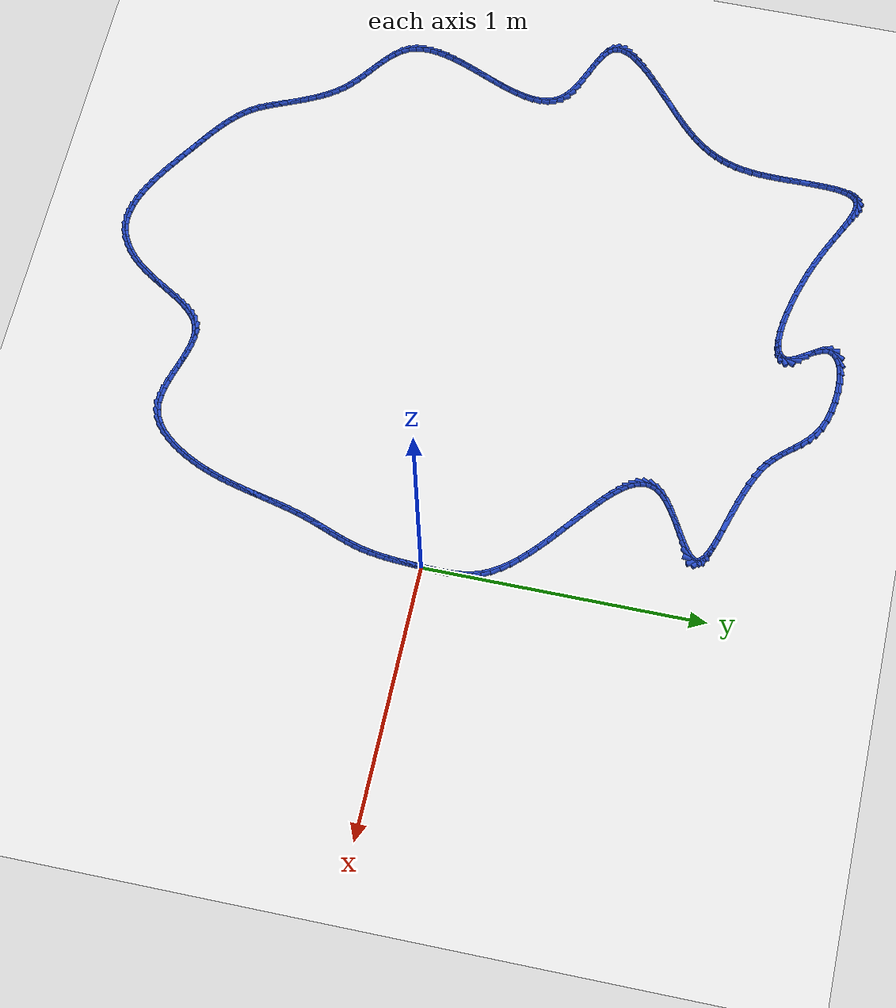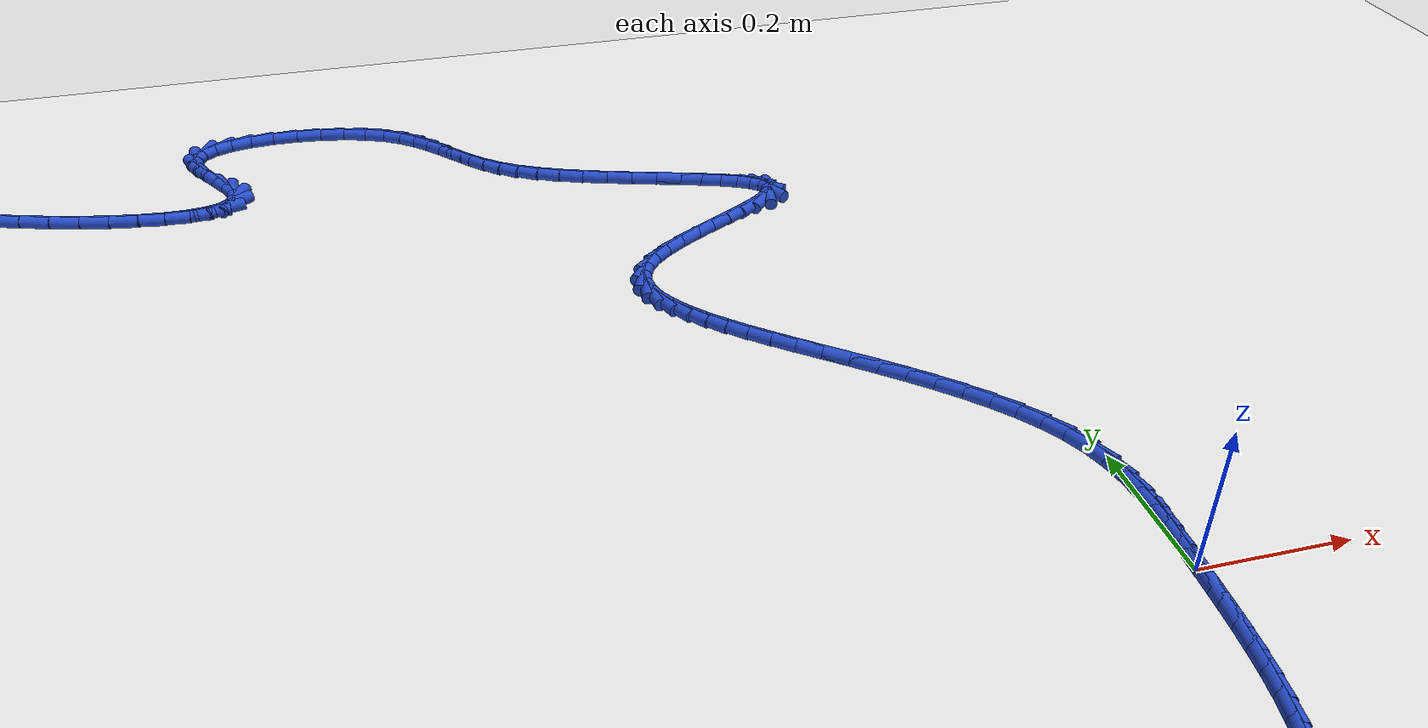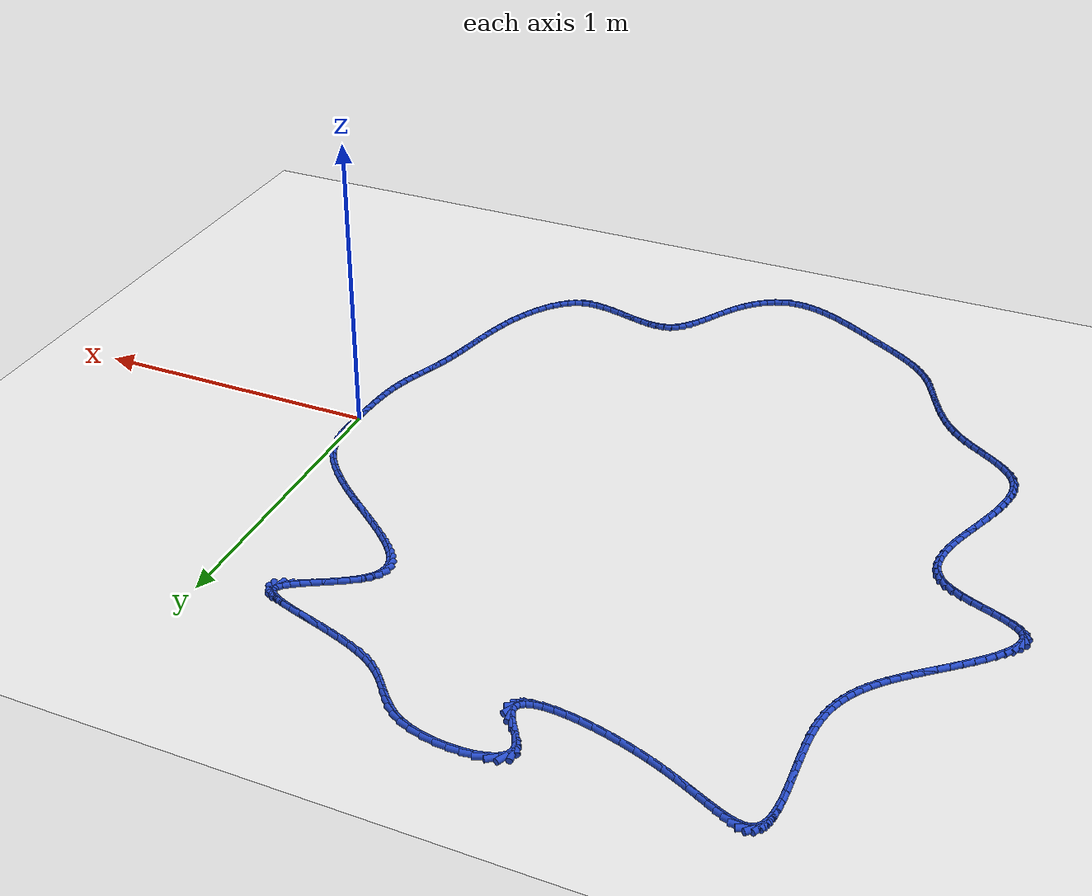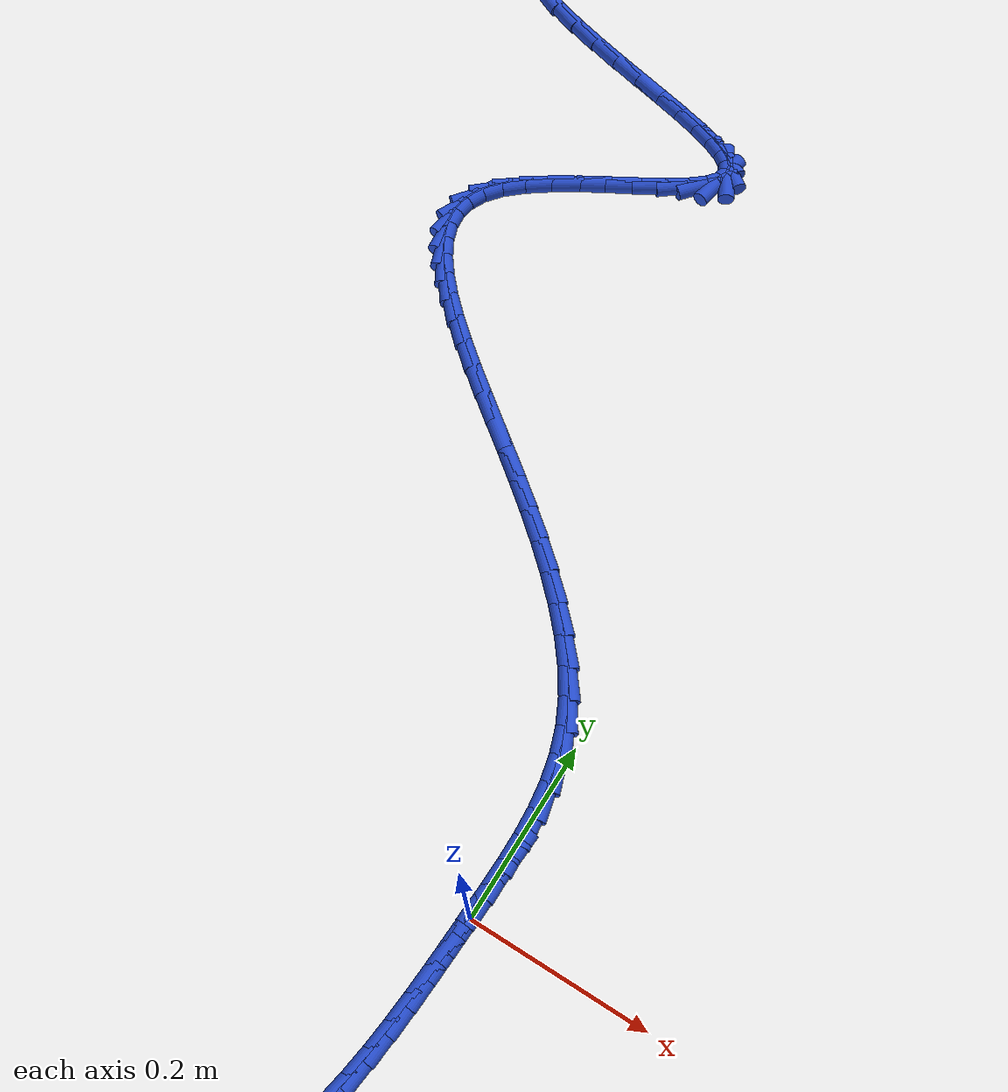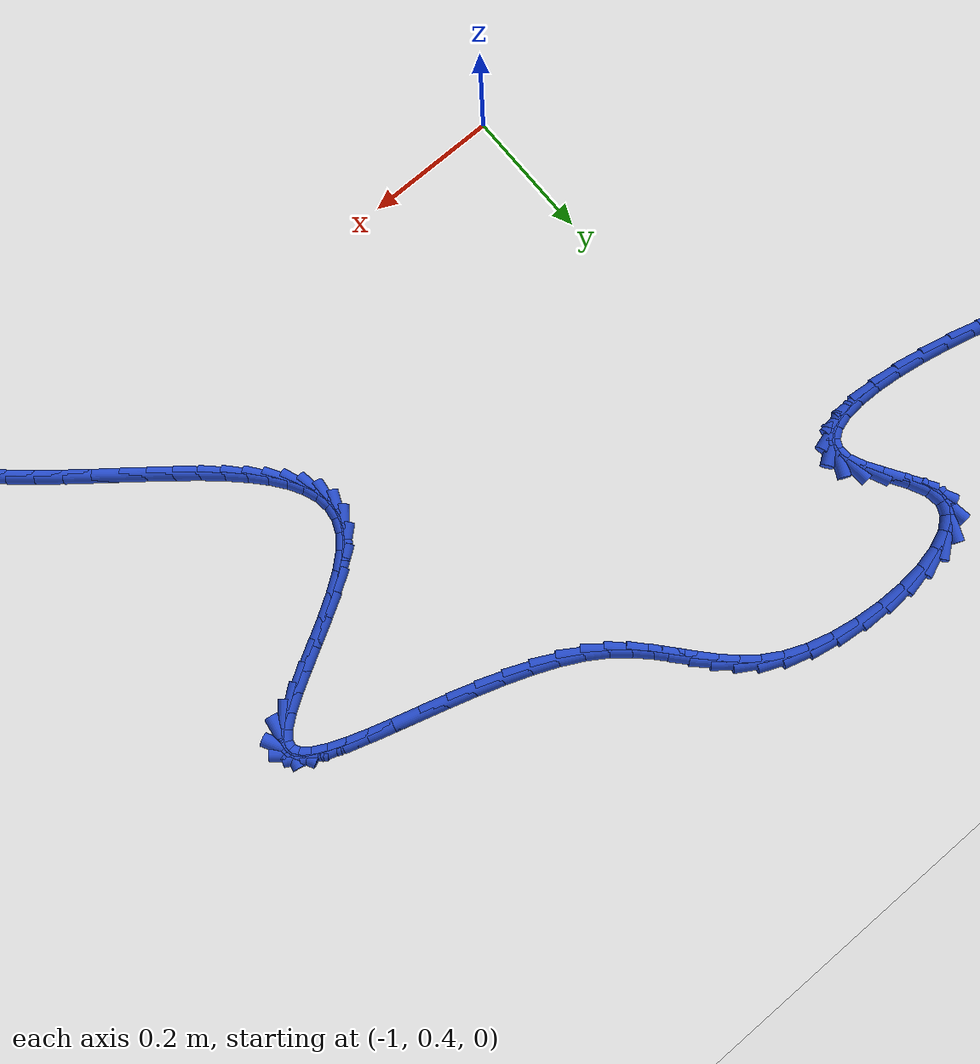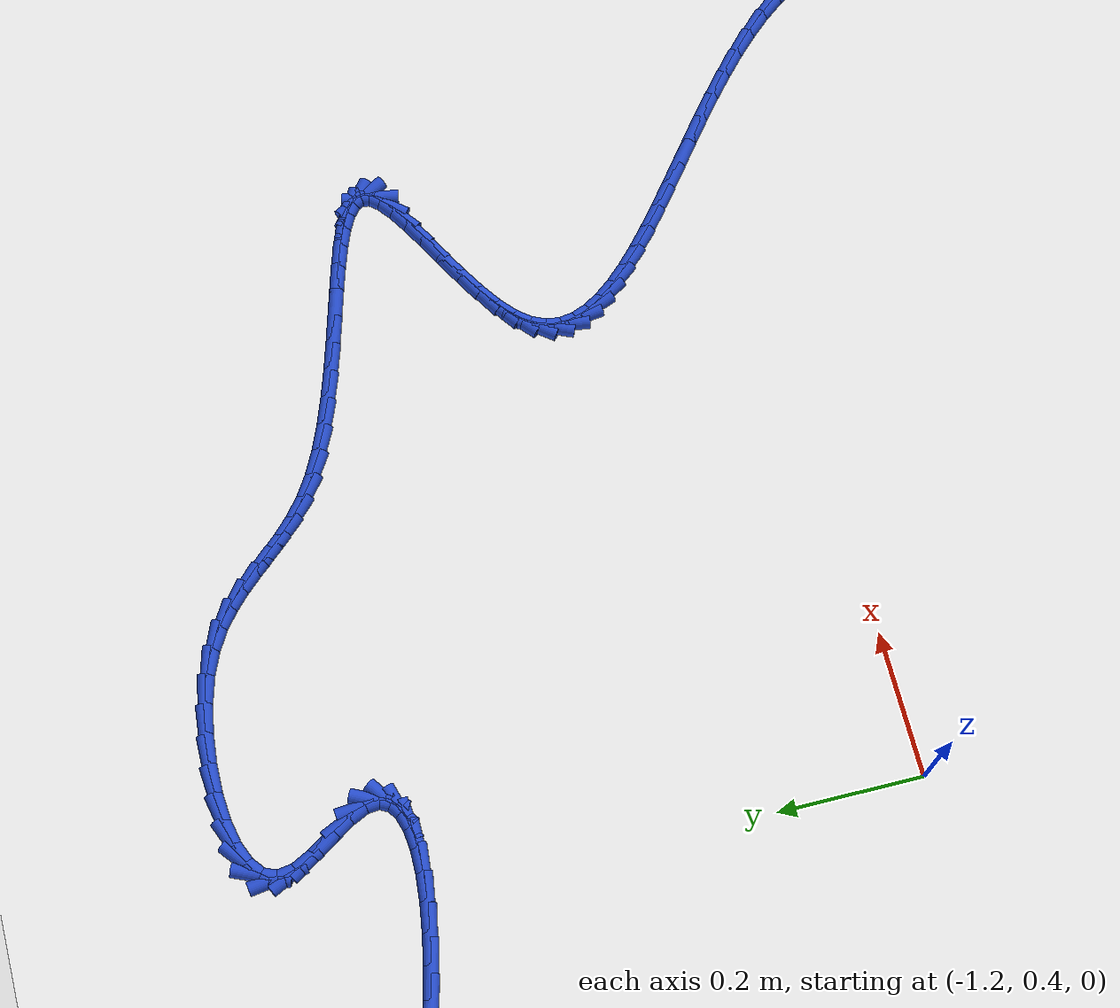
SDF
<sdf version="1.6">
 <world name="default">
  <light name="sun" type="directional">
   <pose>0 0 10 0 -0 0</pose>
   <diffuse>0.8 0.8 0.8 1</diffuse>
   <specular>0.2 0.2 0.2 1</specular>
   <attenuation>
    <range>1000</range>
    <constant>0.9</constant>
    <linear>0.01</linear>
    <quadratic>0.001</quadratic>
   </attenuation>
   <direction>-0.5 0.1 -0.9</direction>
  </light>
  <model name="ground_plane">
   <static>1</static>
   <link name="link">
    <collision name="collision">
     <geometry><plane><normal>0 0 1</normal><size>100 100</size></plane></geometry>
     <surface><friction><ode><mu>100</mu><mu2>50</mu2></ode></friction></surface>
    </collision>
    <visual name="visual">
     <cast_shadows>0</cast_shadows>
     <geometry><plane><normal>0 0 1</normal><size>100 100</size></plane></geometry>
     <material>
      <script><uri>file://media/materials/scripts/gazebo.material</uri><name>Gazebo/WhiteGlow</name></script>
     </material>
    </visual>
   </link>
  </model>
  <gravity>0 0 -9.8</gravity>
  <magnetic_field>6e-06 2.3e-05 -4.2e-05</magnetic_field>
  <atmosphere type="adiabatic"/>
  <physics name="default_physics" default="0" type="ode">
   <max_step_size>0.001</max_step_size>
   <real_time_factor>1</real_time_factor>
   <real_time_update_rate>1000</real_time_update_rate>
  </physics>
  <scene><ambient>0.4 0.4 0.4 1</ambient><background>0.7 0.7 0.7 1</background><shadows>1</shadows></scene>
  <spherical_coordinates>
   <surface_model>EARTH_WGS84</surface_model>
   <latitude_deg>0</latitude_deg>
   <longitude_deg>0</longitude_deg>
   <elevation>0</elevation>
   <heading_deg>0</heading_deg>
  </spherical_coordinates>
  <model name="line">
   <link name="link_0">
    <pose>4.7704895589362195e-18 0.0 0.01 0 1.57 1.5209005659295367</pose>
    <collision name="collision">
     <geometry><cylinder><radius>0.01</radius><length>0.08</length></cylinder></geometry>
    </collision>
    <visual name="visual">
     <material>
      <script><name>Gazebo/Blue</name><uri>file://media/materials/scripts/gazebo.material</uri></script>
     </material>
     <geometry><cylinder><radius>0.01</radius><length>0.08</length></cylinder></geometry>
    </visual>
   </link>
   <link name="link_1">
    <pose>0.0015284782496837674 0.03060800328766565 0.01 0 1.57 1.537293580630483</pose>
    <collision name="collision">
     <geometry><cylinder><radius>0.01</radius><length>0.08</length></cylinder></geometry>
    </collision>
    <visual name="visual">
     <material>
      <script><name>Gazebo/Blue</name><uri>file://media/materials/scripts/gazebo.material</uri></script>
     </material>
     <geometry><cylinder><radius>0.01</radius><length>0.08</length></cylinder></geometry>
    </visual>
   </link>
   <link name="link_2">
    <pose>0.0025532625696801543 0.061184627325808004 0.01 0 1.57 -1.569080206977457</pose>
    <collision name="collision">
     <geometry><cylinder><radius>0.01</radius><length>0.08</length></cylinder></geometry>
    </collision>
    <visual name="visual">
     <material>
      <script><name>Gazebo/Blue</name><uri>file://media/materials/scripts/gazebo.material</uri></script>
     </material>
     <geometry><cylinder><radius>0.01</radius><length>0.08</length></cylinder></geometry>
    </visual>
   </link>
   <link name="link_3">
    <pose>0.002500974813831004 0.09165319017757491 0.01 0 1.57 -1.5146294672387601</pose>
    <collision name="collision">
     <geometry><cylinder><radius>0.01</radius><length>0.08</length></cylinder></geometry>
    </collision>
    <visual name="visual">
     <material>
      <script><name>Gazebo/Blue</name><uri>file://media/materials/scripts/gazebo.material</uri></script>
     </material>
     <geometry><cylinder><radius>0.01</radius><length>0.08</length></cylinder></geometry>
    </visual>
   </link>
   <link name="link_4">
    <pose>0.0007982368359781573 0.12193700990611418 0.01 0 1.57 -1.4407465822392564</pose>
    <collision name="collision">
     <geometry><cylinder><radius>0.01</radius><length>0.08</length></cylinder></geometry>
    </collision>
    <visual name="visual">
     <material>
      <script><name>Gazebo/Blue</name><uri>file://media/materials/scripts/gazebo.material</uri></script>
     </material>
     <geometry><cylinder><radius>0.01</radius><length>0.08</length></cylinder></geometry>
    </visual>
   </link>
   <link name="link_5">
    <pose>-0.003128329510036545 0.15195940457457374 0.01 0 1.57 -1.3480455954679698</pose>
    <collision name="collision">
     <geometry><cylinder><radius>0.01</radius><length>0.08</length></cylinder></geometry>
    </collision>
    <visual name="visual">
     <material>
      <script><name>Gazebo/Blue</name><uri>file://media/materials/scripts/gazebo.material</uri></script>
     </material>
     <geometry><cylinder><radius>0.01</radius><length>0.08</length></cylinder></geometry>
    </visual>
   </link>
   <link name="link_6">
    <pose>-0.009852102370371266 0.18164369224610138 0.01 0 1.57 -1.2386932895417684</pose>
    <collision name="collision">
     <geometry><cylinder><radius>0.01</radius><length>0.08</length></cylinder></geometry>
    </collision>
    <visual name="visual">
     <material>
      <script><name>Gazebo/Blue</name><uri>file://media/materials/scripts/gazebo.material</uri></script>
     </material>
     <geometry><cylinder><radius>0.01</radius><length>0.08</length></cylinder></geometry>
    </visual>
   </link>
   <link name="link_7">
    <pose>-0.01994645989118416 0.21091319098384492 0.01 0 1.57 -1.1180624288054297</pose>
    <collision name="collision">
     <geometry><cylinder><radius>0.01</radius><length>0.08</length></cylinder></geometry>
    </collision>
    <visual name="visual">
     <material>
      <script><name>Gazebo/Blue</name><uri>file://media/materials/scripts/gazebo.material</uri></script>
     </material>
     <geometry><cylinder><radius>0.01</radius><length>0.08</length></cylinder></geometry>
    </visual>
   </link>
   <link name="link_8">
    <pose>-0.0339465029595011 0.23969431836833222 0.01 0 1.57 -1.0071411976336728</pose>
    <collision name="collision">
     <geometry><cylinder><radius>0.01</radius><length>0.08</length></cylinder></geometry>
    </collision>
    <visual name="visual">
     <material>
      <script><name>Gazebo/Blue</name><uri>file://media/materials/scripts/gazebo.material</uri></script>
     </material>
     <geometry><cylinder><radius>0.01</radius><length>0.08</length></cylinder></geometry>
    </visual>
   </link>
   <link name="link_9">
    <pose>-0.05181196645920728 0.26796008248753433 0.01 0 1.57 -0.9175272400275986</pose>
    <collision name="collision">
     <geometry><cylinder><radius>0.01</radius><length>0.08</length></cylinder></geometry>
    </collision>
    <visual name="visual">
     <material>
      <script><name>Gazebo/Blue</name><uri>file://media/materials/scripts/gazebo.material</uri></script>
     </material>
     <geometry><cylinder><radius>0.01</radius><length>0.08</length></cylinder></geometry>
    </visual>
   </link>
   <link name="link_10">
    <pose>-0.07305832109058072 0.2957194659111271 0.01 0 1.57 -0.8462580177132405</pose>
    <collision name="collision">
     <geometry><cylinder><radius>0.01</radius><length>0.08</length></cylinder></geometry>
    </collision>
    <visual name="visual">
     <material>
      <script><name>Gazebo/Blue</name><uri>file://media/materials/scripts/gazebo.material</uri></script>
     </material>
     <geometry><cylinder><radius>0.01</radius><length>0.08</length></cylinder></geometry>
    </visual>
   </link>
   <link name="link_11">
    <pose>-0.09718953150126901 0.32298238291630377 0.01 0 1.57 -0.7902077203371549</pose>
    <collision name="collision">
     <geometry><cylinder><radius>0.01</radius><length>0.08</length></cylinder></geometry>
    </collision>
    <visual name="visual">
     <material>
      <script><name>Gazebo/Blue</name><uri>file://media/materials/scripts/gazebo.material</uri></script>
     </material>
     <geometry><cylinder><radius>0.01</radius><length>0.08</length></cylinder></geometry>
    </visual>
   </link>
   <link name="link_12">
    <pose>-0.1237095623389198 0.349758747780258 0.01 0 1.57 -0.7467956951377155</pose>
    <collision name="collision">
     <geometry><cylinder><radius>0.01</radius><length>0.08</length></cylinder></geometry>
    </collision>
    <visual name="visual">
     <material>
      <script><name>Gazebo/Blue</name><uri>file://media/materials/scripts/gazebo.material</uri></script>
     </material>
     <geometry><cylinder><radius>0.01</radius><length>0.08</length></cylinder></geometry>
    </visual>
   </link>
   <link name="link_13">
    <pose>-0.15212237825118077 0.3760584747801834 0.01 0 1.57 -0.7140532744991808</pose>
    <collision name="collision">
     <geometry><cylinder><radius>0.01</radius><length>0.08</length></cylinder></geometry>
    </collision>
    <visual name="visual">
     <material>
      <script><name>Gazebo/Blue</name><uri>file://media/materials/scripts/gazebo.material</uri></script>
     </material>
     <geometry><cylinder><radius>0.01</radius><length>0.08</length></cylinder></geometry>
    </visual>
   </link>
   <link name="link_14">
    <pose>-0.18193194388569936 0.4018914781932733 0.01 0 1.57 -0.6905786795140608</pose>
    <collision name="collision">
     <geometry><cylinder><radius>0.01</radius><length>0.08</length></cylinder></geometry>
    </collision>
    <visual name="visual">
     <material>
      <script><name>Gazebo/Blue</name><uri>file://media/materials/scripts/gazebo.material</uri></script>
     </material>
     <geometry><cylinder><radius>0.01</radius><length>0.08</length></cylinder></geometry>
    </visual>
   </link>
   <link name="link_15">
    <pose>-0.21264222389012347 0.42726767229672147 0.01 0 1.57 -0.6754721019940143</pose>
    <collision name="collision">
     <geometry><cylinder><radius>0.01</radius><length>0.08</length></cylinder></geometry>
    </collision>
    <visual name="visual">
     <material>
      <script><name>Gazebo/Blue</name><uri>file://media/materials/scripts/gazebo.material</uri></script>
     </material>
     <geometry><cylinder><radius>0.01</radius><length>0.08</length></cylinder></geometry>
    </visual>
   </link>
   <link name="link_16">
    <pose>-0.2437571829121006 0.4521969713677213 0.01 0 1.57 -0.6682894268690722</pose>
    <collision name="collision">
     <geometry><cylinder><radius>0.01</radius><length>0.08</length></cylinder></geometry>
    </collision>
    <visual name="visual">
     <material>
      <script><name>Gazebo/Blue</name><uri>file://media/materials/scripts/gazebo.material</uri></script>
     </material>
     <geometry><cylinder><radius>0.01</radius><length>0.08</length></cylinder></geometry>
    </visual>
   </link>
   <link name="link_17">
    <pose>-0.2747807855992784 0.4766892896834665 0.01 0 1.57 -0.6690310822193424</pose>
    <collision name="collision">
     <geometry><cylinder><radius>0.01</radius><length>0.08</length></cylinder></geometry>
    </collision>
    <visual name="visual">
     <material>
      <script><name>Gazebo/Blue</name><uri>file://media/materials/scripts/gazebo.material</uri></script>
     </material>
     <geometry><cylinder><radius>0.01</radius><length>0.08</length></cylinder></geometry>
    </visual>
   </link>
   <link name="link_18">
    <pose>-0.3052169965993044 0.5007545415211503 0.01 0 1.57 -0.6781771857134884</pose>
    <collision name="collision">
     <geometry><cylinder><radius>0.01</radius><length>0.08</length></cylinder></geometry>
    </collision>
    <visual name="visual">
     <material>
      <script><name>Gazebo/Blue</name><uri>file://media/materials/scripts/gazebo.material</uri></script>
     </material>
     <geometry><cylinder><radius>0.01</radius><length>0.08</length></cylinder></geometry>
    </visual>
   </link>
   <link name="link_19">
    <pose>-0.33456978055982645 0.5244026411579666 0.01 0 1.57 -0.6967837894188746</pose>
    <collision name="collision">
     <geometry><cylinder><radius>0.01</radius><length>0.08</length></cylinder></geometry>
    </collision>
    <visual name="visual">
     <material>
      <script><name>Gazebo/Blue</name><uri>file://media/materials/scripts/gazebo.material</uri></script>
     </material>
     <geometry><cylinder><radius>0.01</radius><length>0.08</length></cylinder></geometry>
    </visual>
   </link>
   <link name="link_20">
    <pose>-0.36234310212849197 0.5476435028711086 0.01 0 1.57 -0.726664686968046</pose>
    <collision name="collision">
     <geometry><cylinder><radius>0.01</radius><length>0.08</length></cylinder></geometry>
    </collision>
    <visual name="visual">
     <material>
      <script><name>Gazebo/Blue</name><uri>file://media/materials/scripts/gazebo.material</uri></script>
     </material>
     <geometry><cylinder><radius>0.01</radius><length>0.08</length></cylinder></geometry>
    </visual>
   </link>
   <link name="link_21">
    <pose>-0.38804092595294865 0.5704870409377701 0.01 0 1.57 -0.7706970185485295</pose>
    <collision name="collision">
     <geometry><cylinder><radius>0.01</radius><length>0.08</length></cylinder></geometry>
    </collision>
    <visual name="visual">
     <material>
      <script><name>Gazebo/Blue</name><uri>file://media/materials/scripts/gazebo.material</uri></script>
     </material>
     <geometry><cylinder><radius>0.01</radius><length>0.08</length></cylinder></geometry>
    </visual>
   </link>
   <link name="link_22">
    <pose>-0.41116721668084416 0.5929431696351447 0.01 0 1.57 -0.8332978531784716</pose>
    <collision name="collision">
     <geometry><cylinder><radius>0.01</radius><length>0.08</length></cylinder></geometry>
    </collision>
    <visual name="visual">
     <material>
      <script><name>Gazebo/Blue</name><uri>file://media/materials/scripts/gazebo.material</uri></script>
     </material>
     <geometry><cylinder><radius>0.01</radius><length>0.08</length></cylinder></geometry>
    </visual>
   </link>
   <link name="link_23">
    <pose>-0.43122593895982597 0.6150218032404253 0.01 0 1.57 -0.9210800979003577</pose>
    <collision name="collision">
     <geometry><cylinder><radius>0.01</radius><length>0.08</length></cylinder></geometry>
    </collision>
    <visual name="visual">
     <material>
      <script><name>Gazebo/Blue</name><uri>file://media/materials/scripts/gazebo.material</uri></script>
     </material>
     <geometry><cylinder><radius>0.01</radius><length>0.08</length></cylinder></geometry>
    </visual>
   </link>
   <link name="link_24">
    <pose>-0.4477210574375421 0.6367328560308064 0.01 0 1.57 -1.0434441614694652</pose>
    <collision name="collision">
     <geometry><cylinder><radius>0.01</radius><length>0.08</length></cylinder></geometry>
    </collision>
    <visual name="visual">
     <material>
      <script><name>Gazebo/Blue</name><uri>file://media/materials/scripts/gazebo.material</uri></script>
     </material>
     <geometry><cylinder><radius>0.01</radius><length>0.08</length></cylinder></geometry>
    </visual>
   </link>
   <link name="link_25">
    <pose>-0.46015653676163987 0.6580862422834808 0.01 0 1.57 -1.2119133022652704</pose>
    <collision name="collision">
     <geometry><cylinder><radius>0.01</radius><length>0.08</length></cylinder></geometry>
    </collision>
    <visual name="visual">
     <material>
      <script><name>Gazebo/Blue</name><uri>file://media/materials/scripts/gazebo.material</uri></script>
     </material>
     <geometry><cylinder><radius>0.01</radius><length>0.08</length></cylinder></geometry>
    </visual>
   </link>
   <link name="link_26">
    <pose>-0.4680363415797669 0.6790918762756425 0.01 0 1.57 -1.4348050715899647</pose>
    <collision name="collision">
     <geometry><cylinder><radius>0.01</radius><length>0.08</length></cylinder></geometry>
    </collision>
    <visual name="visual">
     <material>
      <script><name>Gazebo/Blue</name><uri>file://media/materials/scripts/gazebo.material</uri></script>
     </material>
     <geometry><cylinder><radius>0.01</radius><length>0.08</length></cylinder></geometry>
    </visual>
   </link>
   <link name="link_27">
    <pose>-0.47086443653957105 0.6997596722844847 0.01 0 1.57 1.4378744392433662</pose>
    <collision name="collision">
     <geometry><cylinder><radius>0.01</radius><length>0.08</length></cylinder></geometry>
    </collision>
    <visual name="visual">
     <material>
      <script><name>Gazebo/Blue</name><uri>file://media/materials/scripts/gazebo.material</uri></script>
     </material>
     <geometry><cylinder><radius>0.01</radius><length>0.08</length></cylinder></geometry>
    </visual>
   </link>
   <link name="link_28">
    <pose>-0.46814478628869965 0.720099544587201 0.01 0 1.57 1.1582238367129798</pose>
    <collision name="collision">
     <geometry><cylinder><radius>0.01</radius><length>0.08</length></cylinder></geometry>
    </collision>
    <visual name="visual">
     <material>
      <script><name>Gazebo/Blue</name><uri>file://media/materials/scripts/gazebo.material</uri></script>
     </material>
     <geometry><cylinder><radius>0.01</radius><length>0.08</length></cylinder></geometry>
    </visual>
   </link>
   <link name="link_29">
    <pose>-0.4593813554748005 0.740121407460985 0.01 0 1.57 0.9107008182601583</pose>
    <collision name="collision">
     <geometry><cylinder><radius>0.01</radius><length>0.08</length></cylinder></geometry>
    </collision>
    <visual name="visual">
     <material>
      <script><name>Gazebo/Blue</name><uri>file://media/materials/scripts/gazebo.material</uri></script>
     </material>
     <geometry><cylinder><radius>0.01</radius><length>0.08</length></cylinder></geometry>
    </visual>
   </link>
   <link name="link_30">
    <pose>-0.44407839573635316 0.7598351630717289 0.01 0 1.57 0.7261743571495091</pose>
    <collision name="collision">
     <geometry><cylinder><radius>0.01</radius><length>0.08</length></cylinder></geometry>
    </collision>
    <visual name="visual">
     <material>
      <script><name>Gazebo/Blue</name><uri>file://media/materials/scripts/gazebo.material</uri></script>
     </material>
     <geometry><cylinder><radius>0.01</radius><length>0.08</length></cylinder></geometry>
    </visual>
   </link>
   <link name="link_31">
    <pose>-0.4222390106282682 0.779229661533089 0.01 0 1.57 0.6158409909039841</pose>
    <collision name="collision">
     <geometry><cylinder><radius>0.01</radius><length>0.08</length></cylinder></geometry>
    </collision>
    <visual name="visual">
     <material>
      <script><name>Gazebo/Blue</name><uri>file://media/materials/scripts/gazebo.material</uri></script>
     </material>
     <geometry><cylinder><radius>0.01</radius><length>0.08</length></cylinder></geometry>
    </visual>
   </link>
   <link name="link_32">
    <pose>-0.39538982176992105 0.7982294589652185 0.01 0 1.57 0.5523717494121562</pose>
    <collision name="collision">
     <geometry><cylinder><radius>0.01</radius><length>0.08</length></cylinder></geometry>
    </collision>
    <visual name="visual">
     <material>
      <script><name>Gazebo/Blue</name><uri>file://media/materials/scripts/gazebo.material</uri></script>
     </material>
     <geometry><cylinder><radius>0.01</radius><length>0.08</length></cylinder></geometry>
    </visual>
   </link>
   <link name="link_33">
    <pose>-0.3653472763014694 0.8167468805600087 0.01 0 1.57 0.5189876670722925</pose>
    <collision name="collision">
     <geometry><cylinder><radius>0.01</radius><length>0.08</length></cylinder></geometry>
    </collision>
    <visual name="visual">
     <material>
      <script><name>Gazebo/Blue</name><uri>file://media/materials/scripts/gazebo.material</uri></script>
     </material>
     <geometry><cylinder><radius>0.01</radius><length>0.08</length></cylinder></geometry>
    </visual>
   </link>
   <link name="link_34">
    <pose>-0.33392782136307136 0.8346942515093518 0.01 0 1.57 0.5090346806755731</pose>
    <collision name="collision">
     <geometry><cylinder><radius>0.01</radius><length>0.08</length></cylinder></geometry>
    </collision>
    <visual name="visual">
     <material>
      <script><name>Gazebo/Blue</name><uri>file://media/materials/scripts/gazebo.material</uri></script>
     </material>
     <geometry><cylinder><radius>0.01</radius><length>0.08</length></cylinder></geometry>
    </visual>
   </link>
   <link name="link_35">
    <pose>-0.30294790409488453 0.8519838970051395 0.01 0 1.57 0.522566140537982</pose>
    <collision name="collision">
     <geometry><cylinder><radius>0.01</radius><length>0.08</length></cylinder></geometry>
    </collision>
    <visual name="visual">
     <material>
      <script><name>Gazebo/Blue</name><uri>file://media/materials/scripts/gazebo.material</uri></script>
     </material>
     <geometry><cylinder><radius>0.01</radius><length>0.08</length></cylinder></geometry>
    </visual>
   </link>
   <link name="link_36">
    <pose>-0.274223971637067 0.8685281422392639 0.01 0 1.57 0.5674175865803455</pose>
    <collision name="collision">
     <geometry><cylinder><radius>0.01</radius><length>0.08</length></cylinder></geometry>
    </collision>
    <visual name="visual">
     <material>
      <script><name>Gazebo/Blue</name><uri>file://media/materials/scripts/gazebo.material</uri></script>
     </material>
     <geometry><cylinder><radius>0.01</radius><length>0.08</length></cylinder></geometry>
    </visual>
   </link>
   <link name="link_37">
    <pose>-0.24957247112977649 0.8842393124036169 0.01 0 1.57 0.6675609005205563</pose>
    <collision name="collision">
     <geometry><cylinder><radius>0.01</radius><length>0.08</length></cylinder></geometry>
    </collision>
    <visual name="visual">
     <material>
      <script><name>Gazebo/Blue</name><uri>file://media/materials/scripts/gazebo.material</uri></script>
     </material>
     <geometry><cylinder><radius>0.01</radius><length>0.08</length></cylinder></geometry>
    </visual>
   </link>
   <link name="link_38">
    <pose>-0.23080984971317092 0.8990297326900901 0.01 0 1.57 0.8946488542385334</pose>
    <collision name="collision">
     <geometry><cylinder><radius>0.01</radius><length>0.08</length></cylinder></geometry>
    </collision>
    <visual name="visual">
     <material>
      <script><name>Gazebo/Blue</name><uri>file://media/materials/scripts/gazebo.material</uri></script>
     </material>
     <geometry><cylinder><radius>0.01</radius><length>0.08</length></cylinder></geometry>
    </visual>
   </link>
   <link name="link_39">
    <pose>-0.2197524146927471 0.9128117428025377 0.01 0 1.57 1.4077720821595603</pose>
    <collision name="collision">
     <geometry><cylinder><radius>0.01</radius><length>0.08</length></cylinder></geometry>
    </collision>
    <visual name="visual">
     <material>
      <script><name>Gazebo/Blue</name><uri>file://media/materials/scripts/gazebo.material</uri></script>
     </material>
     <geometry><cylinder><radius>0.01</radius><length>0.08</length></cylinder></geometry>
    </visual>
   </link>
   <link name="link_40">
    <pose>-0.21765621709960623 0.9255558255258186 0.01 0 1.57 -1.0835760126418106</pose>
    <collision name="collision">
     <geometry><cylinder><radius>0.01</radius><length>0.08</length></cylinder></geometry>
    </collision>
    <visual name="visual">
     <material>
      <script><name>Gazebo/Blue</name><uri>file://media/materials/scripts/gazebo.material</uri></script>
     </material>
     <geometry><cylinder><radius>0.01</radius><length>0.08</length></cylinder></geometry>
    </visual>
   </link>
   <link name="link_41">
    <pose>-0.2239435937431828 0.9374227654752215 0.01 0 1.57 -0.6842014545667056</pose>
    <collision name="collision">
     <geometry><cylinder><radius>0.01</radius><length>0.08</length></cylinder></geometry>
    </collision>
    <visual name="visual">
     <material>
      <script><name>Gazebo/Blue</name><uri>file://media/materials/scripts/gazebo.material</uri></script>
     </material>
     <geometry><cylinder><radius>0.01</radius><length>0.08</length></cylinder></geometry>
    </visual>
   </link>
   <link name="link_42">
    <pose>-0.2376623129985314 0.9486122197674546 0.01 0 1.57 -0.4876204432883087</pose>
    <collision name="collision">
     <geometry><cylinder><radius>0.01</radius><length>0.08</length></cylinder></geometry>
    </collision>
    <visual name="visual">
     <material>
      <script><name>Gazebo/Blue</name><uri>file://media/materials/scripts/gazebo.material</uri></script>
     </material>
     <geometry><cylinder><radius>0.01</radius><length>0.08</length></cylinder></geometry>
    </visual>
   </link>
   <link name="link_43">
    <pose>-0.2578601432407067 0.959323845519227 0.01 0 1.57 -0.3853083352462518</pose>
    <collision name="collision">
     <geometry><cylinder><radius>0.01</radius><length>0.08</length></cylinder></geometry>
    </collision>
    <visual name="visual">
     <material>
      <script><name>Gazebo/Blue</name><uri>file://media/materials/scripts/gazebo.material</uri></script>
     </material>
     <geometry><cylinder><radius>0.01</radius><length>0.08</length></cylinder></geometry>
    </visual>
   </link>
   <link name="link_44">
    <pose>-0.28358485284476365 0.9697572998472477 0.01 0 1.57 -0.32931031113262454</pose>
    <collision name="collision">
     <geometry><cylinder><radius>0.01</radius><length>0.08</length></cylinder></geometry>
    </collision>
    <visual name="visual">
     <material>
      <script><name>Gazebo/Blue</name><uri>file://media/materials/scripts/gazebo.material</uri></script>
     </material>
     <geometry><cylinder><radius>0.01</radius><length>0.08</length></cylinder></geometry>
    </visual>
   </link>
   <link name="link_45">
    <pose>-0.31388421018575646 0.9801122398682247 0.01 0 1.57 -0.2995384758358758</pose>
    <collision name="collision">
     <geometry><cylinder><radius>0.01</radius><length>0.08</length></cylinder></geometry>
    </collision>
    <visual name="visual">
     <material>
      <script><name>Gazebo/Blue</name><uri>file://media/materials/scripts/gazebo.material</uri></script>
     </material>
     <geometry><cylinder><radius>0.01</radius><length>0.08</length></cylinder></geometry>
    </visual>
   </link>
   <link name="link_46">
    <pose>-0.34780598363874027 0.9905883226988667 0.01 0 1.57 -0.28692004466132665</pose>
    <collision name="collision">
     <geometry><cylinder><radius>0.01</radius><length>0.08</length></cylinder></geometry>
    </collision>
    <visual name="visual">
     <material>
      <script><name>Gazebo/Blue</name><uri>file://media/materials/scripts/gazebo.material</uri></script>
     </material>
     <geometry><cylinder><radius>0.01</radius><length>0.08</length></cylinder></geometry>
    </visual>
   </link>
   <link name="link_47">
    <pose>-0.38439794157876916 1.001385205455882 0.01 0 1.57 -0.2872455026072532</pose>
    <collision name="collision">
     <geometry><cylinder><radius>0.01</radius><length>0.08</length></cylinder></geometry>
    </collision>
    <visual name="visual">
     <material>
      <script><name>Gazebo/Blue</name><uri>file://media/materials/scripts/gazebo.material</uri></script>
     </material>
     <geometry><cylinder><radius>0.01</radius><length>0.08</length></cylinder></geometry>
    </visual>
   </link>
   <link name="link_48">
    <pose>-0.42270785238089836 1.0127025452559804 0.01 0 1.57 -0.2988304589437269</pose>
    <collision name="collision">
     <geometry><cylinder><radius>0.01</radius><length>0.08</length></cylinder></geometry>
    </collision>
    <visual name="visual">
     <material>
      <script><name>Gazebo/Blue</name><uri>file://media/materials/scripts/gazebo.material</uri></script>
     </material>
     <geometry><cylinder><radius>0.01</radius><length>0.08</length></cylinder></geometry>
    </visual>
   </link>
   <link name="link_49">
    <pose>-0.461783484420182 1.0247399992158688 0.01 0 1.57 -0.3216159661815669</pose>
    <collision name="collision">
     <geometry><cylinder><radius>0.01</radius><length>0.08</length></cylinder></geometry>
    </collision>
    <visual name="visual">
     <material>
      <script><name>Gazebo/Blue</name><uri>file://media/materials/scripts/gazebo.material</uri></script>
     </material>
     <geometry><cylinder><radius>0.01</radius><length>0.08</length></cylinder></geometry>
    </visual>
   </link>
   <link name="link_50">
    <pose>-0.5006726060716753 1.0376972244522569 0.01 0 1.57 -0.35691753837155293</pose>
    <collision name="collision">
     <geometry><cylinder><radius>0.01</radius><length>0.08</length></cylinder></geometry>
    </collision>
    <visual name="visual">
     <material>
      <script><name>Gazebo/Blue</name><uri>file://media/materials/scripts/gazebo.material</uri></script>
     </material>
     <geometry><cylinder><radius>0.01</radius><length>0.08</length></cylinder></geometry>
    </visual>
   </link>
   <link name="link_51">
    <pose>-0.5384229857104325 1.051773878081853 0.01 0 1.57 -0.407569088144858</pose>
    <collision name="collision">
     <geometry><cylinder><radius>0.01</radius><length>0.08</length></cylinder></geometry>
    </collision>
    <visual name="visual">
     <material>
      <script><name>Gazebo/Blue</name><uri>file://media/materials/scripts/gazebo.material</uri></script>
     </material>
     <geometry><cylinder><radius>0.01</radius><length>0.08</length></cylinder></geometry>
    </visual>
   </link>
   <link name="link_52">
    <pose>-0.5740823917115083 1.0671696172213658 0.01 0 1.57 -0.4784098817454756</pose>
    <collision name="collision">
     <geometry><cylinder><radius>0.01</radius><length>0.08</length></cylinder></geometry>
    </collision>
    <visual name="visual">
     <material>
      <script><name>Gazebo/Blue</name><uri>file://media/materials/scripts/gazebo.material</uri></script>
     </material>
     <geometry><cylinder><radius>0.01</radius><length>0.08</length></cylinder></geometry>
    </visual>
   </link>
   <link name="link_53">
    <pose>-0.6066985924499573 1.0840840989875034 0.01 0 1.57 -0.5765808142376876</pose>
    <collision name="collision">
     <geometry><cylinder><radius>0.01</radius><length>0.08</length></cylinder></geometry>
    </collision>
    <visual name="visual">
     <material>
      <script><name>Gazebo/Blue</name><uri>file://media/materials/scripts/gazebo.material</uri></script>
     </material>
     <geometry><cylinder><radius>0.01</radius><length>0.08</length></cylinder></geometry>
    </visual>
   </link>
   <link name="link_54">
    <pose>-0.6353402614776684 1.102709561430693 0.01 0 1.57 -0.6883399514578248</pose>
    <collision name="collision">
     <geometry><cylinder><radius>0.01</radius><length>0.08</length></cylinder></geometry>
    </collision>
    <visual name="visual">
     <material>
      <script><name>Gazebo/Blue</name><uri>file://media/materials/scripts/gazebo.material</uri></script>
     </material>
     <geometry><cylinder><radius>0.01</radius><length>0.08</length></cylinder></geometry>
    </visual>
   </link>
   <link name="link_55">
    <pose>-0.6599294588325509 1.1229353831252706 0.01 0 1.57 -0.7789204026373183</pose>
    <collision name="collision">
     <geometry><cylinder><radius>0.01</radius><length>0.08</length></cylinder></geometry>
    </collision>
    <visual name="visual">
     <material>
      <script><name>Gazebo/Blue</name><uri>file://media/materials/scripts/gazebo.material</uri></script>
     </material>
     <geometry><cylinder><radius>0.01</radius><length>0.08</length></cylinder></geometry>
    </visual>
   </link>
   <link name="link_56">
    <pose>-0.6815209600824957 1.1442489517099395 0.01 0 1.57 -0.8366711841736815</pose>
    <collision name="collision">
     <geometry><cylinder><radius>0.01</radius><length>0.08</length></cylinder></geometry>
    </collision>
    <visual name="visual">
     <material>
      <script><name>Gazebo/Blue</name><uri>file://media/materials/scripts/gazebo.material</uri></script>
     </material>
     <geometry><cylinder><radius>0.01</radius><length>0.08</length></cylinder></geometry>
    </visual>
   </link>
   <link name="link_57">
    <pose>-0.7012477197165798 1.1661099098010712 0.01 0 1.57 -0.8555912537976701</pose>
    <collision name="collision">
     <geometry><cylinder><radius>0.01</radius><length>0.08</length></cylinder></geometry>
    </collision>
    <visual name="visual">
     <material>
      <script><name>Gazebo/Blue</name><uri>file://media/materials/scripts/gazebo.material</uri></script>
     </material>
     <geometry><cylinder><radius>0.01</radius><length>0.08</length></cylinder></geometry>
    </visual>
   </link>
   <link name="link_58">
    <pose>-0.7202426922238798 1.1879779000150386 0.01 0 1.57 -0.8329558631543618</pose>
    <collision name="collision">
     <geometry><cylinder><radius>0.01</radius><length>0.08</length></cylinder></geometry>
    </collision>
    <visual name="visual">
     <material>
      <script><name>Gazebo/Blue</name><uri>file://media/materials/scripts/gazebo.material</uri></script>
     </material>
     <geometry><cylinder><radius>0.01</radius><length>0.08</length></cylinder></geometry>
    </visual>
   </link>
   <link name="link_59">
    <pose>-0.739638832093472 1.209312564968213 0.01 0 1.57 -0.769151493976583</pose>
    <collision name="collision">
     <geometry><cylinder><radius>0.01</radius><length>0.08</length></cylinder></geometry>
    </collision>
    <visual name="visual">
     <material>
      <script><name>Gazebo/Blue</name><uri>file://media/materials/scripts/gazebo.material</uri></script>
     </material>
     <geometry><cylinder><radius>0.01</radius><length>0.08</length></cylinder></geometry>
    </visual>
   </link>
   <link name="link_60">
    <pose>-0.7605690938144334 1.2295735472769675 0.01 0 1.57 -0.6687451990214621</pose>
    <collision name="collision">
     <geometry><cylinder><radius>0.01</radius><length>0.08</length></cylinder></geometry>
    </collision>
    <visual name="visual">
     <material>
      <script><name>Gazebo/Blue</name><uri>file://media/materials/scripts/gazebo.material</uri></script>
     </material>
     <geometry><cylinder><radius>0.01</radius><length>0.08</length></cylinder></geometry>
    </visual>
   </link>
   <link name="link_61">
    <pose>-0.7841664318758406 1.2482204895576747 0.01 0 1.57 -0.541870808764979</pose>
    <collision name="collision">
     <geometry><cylinder><radius>0.01</radius><length>0.08</length></cylinder></geometry>
    </collision>
    <visual name="visual">
     <material>
      <script><name>Gazebo/Blue</name><uri>file://media/materials/scripts/gazebo.material</uri></script>
     </material>
     <geometry><cylinder><radius>0.01</radius><length>0.08</length></cylinder></geometry>
    </visual>
   </link>
   <link name="link_62">
    <pose>-0.8115638007667699 1.2647130344267055 0.01 0 1.57 -0.40387303769208976</pose>
    <collision name="collision">
     <geometry><cylinder><radius>0.01</radius><length>0.08</length></cylinder></geometry>
    </collision>
    <visual name="visual">
     <material>
      <script><name>Gazebo/Blue</name><uri>file://media/materials/scripts/gazebo.material</uri></script>
     </material>
     <geometry><cylinder><radius>0.01</radius><length>0.08</length></cylinder></geometry>
    </visual>
   </link>
   <link name="link_63">
    <pose>-0.8438598119882968 1.2785152544241005 0.01 0 1.57 -0.28226828720965347</pose>
    <collision name="collision">
     <geometry><cylinder><radius>0.01</radius><length>0.08</length></cylinder></geometry>
    </collision>
    <visual name="visual">
     <material>
      <script><name>Gazebo/Blue</name><uri>file://media/materials/scripts/gazebo.material</uri></script>
     </material>
     <geometry><cylinder><radius>0.01</radius><length>0.08</length></cylinder></geometry>
    </visual>
   </link>
   <link name="link_64">
    <pose>-0.8808892889451557 1.2892542389129453 0.01 0 1.57 -0.18559314414674144</pose>
    <collision name="collision">
     <geometry><cylinder><radius>0.01</radius><length>0.08</length></cylinder></geometry>
    </collision>
    <visual name="visual">
     <material>
      <script><name>Gazebo/Blue</name><uri>file://media/materials/scripts/gazebo.material</uri></script>
     </material>
     <geometry><cylinder><radius>0.01</radius><length>0.08</length></cylinder></geometry>
    </visual>
   </link>
   <link name="link_65">
    <pose>-0.9208854440851852 1.2967636700630707 0.01 0 1.57 -0.10009182327299232</pose>
    <collision name="collision">
     <geometry><cylinder><radius>0.01</radius><length>0.08</length></cylinder></geometry>
    </collision>
    <visual name="visual">
     <material>
      <script><name>Gazebo/Blue</name><uri>file://media/materials/scripts/gazebo.material</uri></script>
     </material>
     <geometry><cylinder><radius>0.01</radius><length>0.08</length></cylinder></geometry>
    </visual>
   </link>
   <link name="link_66">
    <pose>-0.9619783914536414 1.300890528772233 0.01 0 1.57 -0.014663366430533162</pose>
    <collision name="collision">
     <geometry><cylinder><radius>0.01</radius><length>0.08</length></cylinder></geometry>
    </collision>
    <visual name="visual">
     <material>
      <script><name>Gazebo/Blue</name><uri>file://media/materials/scripts/gazebo.material</uri></script>
     </material>
     <geometry><cylinder><radius>0.01</radius><length>0.08</length></cylinder></geometry>
    </visual>
   </link>
   <link name="link_67">
    <pose>-1.002298245095778 1.3014817959381888 0.01 0 1.57 0.0820236355961028</pose>
    <collision name="collision">
     <geometry><cylinder><radius>0.01</radius><length>0.08</length></cylinder></geometry>
    </collision>
    <visual name="visual">
     <material>
      <script><name>Gazebo/Blue</name><uri>file://media/materials/scripts/gazebo.material</uri></script>
     </material>
     <geometry><cylinder><radius>0.01</radius><length>0.08</length></cylinder></geometry>
    </visual>
   </link>
   <link name="link_68">
    <pose>-1.0399751190568516 1.2983844524586954 0.01 0 1.57 0.2062565605071578</pose>
    <collision name="collision">
     <geometry><cylinder><radius>0.01</radius><length>0.08</length></cylinder></geometry>
    </collision>
    <visual name="visual">
     <material>
      <script><name>Gazebo/Blue</name><uri>file://media/materials/scripts/gazebo.material</uri></script>
     </material>
     <geometry><cylinder><radius>0.01</radius><length>0.08</length></cylinder></geometry>
    </visual>
   </link>
   <link name="link_69">
    <pose>-1.0731391273821163 1.2914454792315089 0.01 0 1.57 0.3876037213641503</pose>
    <collision name="collision">
     <geometry><cylinder><radius>0.01</radius><length>0.08</length></cylinder></geometry>
    </collision>
    <visual name="visual">
     <material>
      <script><name>Gazebo/Blue</name><uri>file://media/materials/scripts/gazebo.material</uri></script>
     </material>
     <geometry><cylinder><radius>0.01</radius><length>0.08</length></cylinder></geometry>
    </visual>
   </link>
   <link name="link_70">
    <pose>-1.099920384116828 1.2805118571543863 0.01 0 1.57 0.6831867642673207</pose>
    <collision name="collision">
     <geometry><cylinder><radius>0.01</radius><length>0.08</length></cylinder></geometry>
    </collision>
    <visual name="visual">
     <material>
      <script><name>Gazebo/Blue</name><uri>file://media/materials/scripts/gazebo.material</uri></script>
     </material>
     <geometry><cylinder><radius>0.01</radius><length>0.08</length></cylinder></geometry>
    </visual>
   </link>
   <link name="link_71">
    <pose>-1.1184490033062418 1.2654305671250845 0.01 0 1.57 1.161574097288925</pose>
    <collision name="collision">
     <geometry><cylinder><radius>0.01</radius><length>0.08</length></cylinder></geometry>
    </collision>
    <visual name="visual">
     <material>
      <script><name>Gazebo/Blue</name><uri>file://media/materials/scripts/gazebo.material</uri></script>
     </material>
     <geometry><cylinder><radius>0.01</radius><length>0.08</length></cylinder></geometry>
    </visual>
   </link>
   <link name="link_72">
    <pose>-1.1268550989956125 1.2460485900413598 0.01 0 1.57 -1.4281970652236406</pose>
    <collision name="collision">
     <geometry><cylinder><radius>0.01</radius><length>0.08</length></cylinder></geometry>
    </collision>
    <visual name="visual">
     <material>
      <script><name>Gazebo/Blue</name><uri>file://media/materials/scripts/gazebo.material</uri></script>
     </material>
     <geometry><cylinder><radius>0.01</radius><length>0.08</length></cylinder></geometry>
    </visual>
   </link>
   <link name="link_73">
    <pose>-1.12344103782641 1.222269444426144 0.01 0 1.57 -1.1134419527512758</pose>
    <collision name="collision">
     <geometry><cylinder><radius>0.01</radius><length>0.08</length></cylinder></geometry>
    </collision>
    <visual name="visual">
     <material>
      <script><name>Gazebo/Blue</name><uri>file://media/materials/scripts/gazebo.material</uri></script>
     </material>
     <geometry><cylinder><radius>0.01</radius><length>0.08</length></cylinder></geometry>
    </visual>
   </link>
   <link name="link_74">
    <pose>-1.1101076443937057 1.1951777530147727 0.01 0 1.57 -1.004112221750847</pose>
    <collision name="collision">
     <geometry><cylinder><radius>0.01</radius><length>0.08</length></cylinder></geometry>
    </collision>
    <visual name="visual">
     <material>
      <script><name>Gazebo/Blue</name><uri>file://media/materials/scripts/gazebo.material</uri></script>
     </material>
     <geometry><cylinder><radius>0.01</radius><length>0.08</length></cylinder></geometry>
    </visual>
   </link>
   <link name="link_75">
    <pose>-1.0921632158349386 1.166976556549778 0.01 0 1.57 -1.0069440193012957</pose>
    <collision name="collision">
     <geometry><cylinder><radius>0.01</radius><length>0.08</length></cylinder></geometry>
    </collision>
    <visual name="visual">
     <material>
      <script><name>Gazebo/Blue</name><uri>file://media/materials/scripts/gazebo.material</uri></script>
     </material>
     <geometry><cylinder><radius>0.01</radius><length>0.08</length></cylinder></geometry>
    </visual>
   </link>
   <link name="link_76">
    <pose>-1.0750500691869016 1.139912884468215 0.01 0 1.57 -1.1403352694862905</pose>
    <collision name="collision">
     <geometry><cylinder><radius>0.01</radius><length>0.08</length></cylinder></geometry>
    </collision>
    <visual name="visual">
     <material>
      <script><name>Gazebo/Blue</name><uri>file://media/materials/scripts/gazebo.material</uri></script>
     </material>
     <geometry><cylinder><radius>0.01</radius><length>0.08</length></cylinder></geometry>
    </visual>
   </link>
   <link name="link_77">
    <pose>-1.0641695966053428 1.116217400907579 0.01 0 1.57 -1.4862586148007373</pose>
    <collision name="collision">
     <geometry><cylinder><radius>0.01</radius><length>0.08</length></cylinder></geometry>
    </collision>
    <visual name="visual">
     <material>
      <script><name>Gazebo/Blue</name><uri>file://media/materials/scripts/gazebo.material</uri></script>
     </material>
     <geometry><cylinder><radius>0.01</radius><length>0.08</length></cylinder></geometry>
    </visual>
   </link>
   <link name="link_78">
    <pose>-1.0625558745513524 1.097174112873986 0.01 0 1.57 1.118738650910807</pose>
    <collision name="collision">
     <geometry><cylinder><radius>0.01</radius><length>0.08</length></cylinder></geometry>
    </collision>
    <visual name="visual">
     <material>
      <script><name>Gazebo/Blue</name><uri>file://media/materials/scripts/gazebo.material</uri></script>
     </material>
     <geometry><cylinder><radius>0.01</radius><length>0.08</length></cylinder></geometry>
    </visual>
   </link>
   <link name="link_79">
    <pose>-1.0696234634662067 1.0826196324781274 0.01 0 1.57 0.6084987038579283</pose>
    <collision name="collision">
     <geometry><cylinder><radius>0.01</radius><length>0.08</length></cylinder></geometry>
    </collision>
    <visual name="visual">
     <material>
      <script><name>Gazebo/Blue</name><uri>file://media/materials/scripts/gazebo.material</uri></script>
     </material>
     <geometry><cylinder><radius>0.01</radius><length>0.08</length></cylinder></geometry>
    </visual>
   </link>
   <link name="link_80">
    <pose>-1.0844813188370368 1.0722683645940845 0.01 0 1.57 0.28751068351842923</pose>
    <collision name="collision">
     <geometry><cylinder><radius>0.01</radius><length>0.08</length></cylinder></geometry>
    </collision>
    <visual name="visual">
     <material>
      <script><name>Gazebo/Blue</name><uri>file://media/materials/scripts/gazebo.material</uri></script>
     </material>
     <geometry><cylinder><radius>0.01</radius><length>0.08</length></cylinder></geometry>
    </visual>
   </link>
   <link name="link_81">
    <pose>-1.1062383961509725 1.0658347140959392 0.01 0 1.57 0.10056372766646694</pose>
    <collision name="collision">
     <geometry><cylinder><radius>0.01</radius><length>0.08</length></cylinder></geometry>
    </collision>
    <visual name="visual">
     <material>
      <script><name>Gazebo/Blue</name><uri>file://media/materials/scripts/gazebo.material</uri></script>
     </material>
     <geometry><cylinder><radius>0.01</radius><length>0.08</length></cylinder></geometry>
    </visual>
   </link>
   <link name="link_82">
    <pose>-1.134003650895144 1.0630330858577721 0.01 0 1.57 -0.01656659060833124</pose>
    <collision name="collision">
     <geometry><cylinder><radius>0.01</radius><length>0.08</length></cylinder></geometry>
    </collision>
    <visual name="visual">
     <material>
      <script><name>Gazebo/Blue</name><uri>file://media/materials/scripts/gazebo.material</uri></script>
     </material>
     <geometry><cylinder><radius>0.01</radius><length>0.08</length></cylinder></geometry>
    </visual>
   </link>
   <link name="link_83">
    <pose>-1.1668860385566817 1.0635778847536657 0.01 0 1.57 -0.09686056270876396</pose>
    <collision name="collision">
     <geometry><cylinder><radius>0.01</radius><length>0.08</length></cylinder></geometry>
    </collision>
    <visual name="visual">
     <material>
      <script><name>Gazebo/Blue</name><uri>file://media/materials/scripts/gazebo.material</uri></script>
     </material>
     <geometry><cylinder><radius>0.01</radius><length>0.08</length></cylinder></geometry>
    </visual>
   </link>
   <link name="link_84">
    <pose>-1.2039945146227147 1.0671835156576999 0.01 0 1.57 -0.15648243109726961</pose>
    <collision name="collision">
     <geometry><cylinder><radius>0.01</radius><length>0.08</length></cylinder></geometry>
    </collision>
    <visual name="visual">
     <material>
      <script><name>Gazebo/Blue</name><uri>file://media/materials/scripts/gazebo.material</uri></script>
     </material>
     <geometry><cylinder><radius>0.01</radius><length>0.08</length></cylinder></geometry>
    </visual>
   </link>
   <link name="link_85">
    <pose>-1.2444380345803745 1.0735643834439572 0.01 0 1.57 -0.20395603534226012</pose>
    <collision name="collision">
     <geometry><cylinder><radius>0.01</radius><length>0.08</length></cylinder></geometry>
    </collision>
    <visual name="visual">
     <material>
      <script><name>Gazebo/Blue</name><uri>file://media/materials/scripts/gazebo.material</uri></script>
     </material>
     <geometry><cylinder><radius>0.01</radius><length>0.08</length></cylinder></geometry>
    </visual>
   </link>
   <link name="link_86">
    <pose>-1.287325553916791 1.0824348929865188 0.01 0 1.57 -0.24422536850942414</pose>
    <collision name="collision">
     <geometry><cylinder><radius>0.01</radius><length>0.08</length></cylinder></geometry>
    </collision>
    <visual name="visual">
     <material>
      <script><name>Gazebo/Blue</name><uri>file://media/materials/scripts/gazebo.material</uri></script>
     </material>
     <geometry><cylinder><radius>0.01</radius><length>0.08</length></cylinder></geometry>
    </visual>
   </link>
   <link name="link_87">
    <pose>-1.3317660281190946 1.0935094491594661 0.01 0 1.57 -0.280483672853604</pose>
    <collision name="collision">
     <geometry><cylinder><radius>0.01</radius><length>0.08</length></cylinder></geometry>
    </collision>
    <visual name="visual">
     <material>
      <script><name>Gazebo/Blue</name><uri>file://media/materials/scripts/gazebo.material</uri></script>
     </material>
     <geometry><cylinder><radius>0.01</radius><length>0.08</length></cylinder></geometry>
    </visual>
   </link>
   <link name="link_88">
    <pose>-1.3768684126744142 1.1065024568368798 0.01 0 1.57 -0.31507938046985046</pose>
    <collision name="collision">
     <geometry><cylinder><radius>0.01</radius><length>0.08</length></cylinder></geometry>
    </collision>
    <visual name="visual">
     <material>
      <script><name>Gazebo/Blue</name><uri>file://media/materials/scripts/gazebo.material</uri></script>
     </material>
     <geometry><cylinder><radius>0.01</radius><length>0.08</length></cylinder></geometry>
    </visual>
   </link>
   <link name="link_89">
    <pose>-1.4217416630698811 1.1211283208928418 0.01 0 1.57 -0.3500404849318791</pose>
    <collision name="collision">
     <geometry><cylinder><radius>0.01</radius><length>0.08</length></cylinder></geometry>
    </collision>
    <visual name="visual">
     <material>
      <script><name>Gazebo/Blue</name><uri>file://media/materials/scripts/gazebo.material</uri></script>
     </material>
     <geometry><cylinder><radius>0.01</radius><length>0.08</length></cylinder></geometry>
    </visual>
   </link>
   <link name="link_90">
    <pose>-1.465494734792625 1.1371014462014335 0.01 0 1.57 -0.3868470926862169</pose>
    <collision name="collision">
     <geometry><cylinder><radius>0.01</radius><length>0.08</length></cylinder></geometry>
    </collision>
    <visual name="visual">
     <material>
      <script><name>Gazebo/Blue</name><uri>file://media/materials/scripts/gazebo.material</uri></script>
     </material>
     <geometry><cylinder><radius>0.01</radius><length>0.08</length></cylinder></geometry>
    </visual>
   </link>
   <link name="link_91">
    <pose>-1.5072711881035423 1.154120088410316 0.01 0 1.57 -0.4191643377994727</pose>
    <collision name="collision">
     <geometry><cylinder><radius>0.01</radius><length>0.08</length></cylinder></geometry>
    </collision>
    <visual name="visual">
     <material>
      <script><name>Gazebo/Blue</name><uri>file://media/materials/scripts/gazebo.material</uri></script>
     </material>
     <geometry><cylinder><radius>0.01</radius><length>0.08</length></cylinder></geometry>
    </visual>
   </link>
   <link name="link_92">
    <pose>-1.5466644424680127 1.1716725645557886 0.01 0 1.57 -0.44105376909332494</pose>
    <collision name="collision">
     <geometry><cylinder><radius>0.01</radius><length>0.08</length></cylinder></geometry>
    </collision>
    <visual name="visual">
     <material>
      <script><name>Gazebo/Blue</name><uri>file://media/materials/scripts/gazebo.material</uri></script>
     </material>
     <geometry><cylinder><radius>0.01</radius><length>0.08</length></cylinder></geometry>
    </visual>
   </link>
   <link name="link_93">
    <pose>-1.5835824651615769 1.1891003996783167 0.01 0 1.57 -0.4510681153422886</pose>
    <collision name="collision">
     <geometry><cylinder><radius>0.01</radius><length>0.08</length></cylinder></geometry>
    </collision>
    <visual name="visual">
     <material>
      <script><name>Gazebo/Blue</name><uri>file://media/materials/scripts/gazebo.material</uri></script>
     </material>
     <geometry><cylinder><radius>0.01</radius><length>0.08</length></cylinder></geometry>
    </visual>
   </link>
   <link name="link_94">
    <pose>-1.6179396752051254 1.2057421079419708 0.01 0 1.57 -0.4468252690239972</pose>
    <collision name="collision">
     <geometry><cylinder><radius>0.01</radius><length>0.08</length></cylinder></geometry>
    </collision>
    <visual name="visual">
     <material>
      <script><name>Gazebo/Blue</name><uri>file://media/materials/scripts/gazebo.material</uri></script>
     </material>
     <geometry><cylinder><radius>0.01</radius><length>0.08</length></cylinder></geometry>
    </visual>
   </link>
   <link name="link_95">
    <pose>-1.649650491619549 1.2209362035108218 0.01 0 1.57 -0.4241307232656373</pose>
    <collision name="collision">
     <geometry><cylinder><radius>0.01</radius><length>0.08</length></cylinder></geometry>
    </collision>
    <visual name="visual">
     <material>
      <script><name>Gazebo/Blue</name><uri>file://media/materials/scripts/gazebo.material</uri></script>
     </material>
     <geometry><cylinder><radius>0.01</radius><length>0.08</length></cylinder></geometry>
    </visual>
   </link>
   <link name="link_96">
    <pose>-1.6786293334257367 1.2340212005489395 0.01 0 1.57 -0.37555044443479474</pose>
    <collision name="collision">
     <geometry><cylinder><radius>0.01</radius><length>0.08</length></cylinder></geometry>
    </collision>
    <visual name="visual">
     <material>
      <script><name>Gazebo/Blue</name><uri>file://media/materials/scripts/gazebo.material</uri></script>
     </material>
     <geometry><cylinder><radius>0.01</radius><length>0.08</length></cylinder></geometry>
    </visual>
   </link>
   <link name="link_97">
    <pose>-1.7047906196445792 1.2443356132203949 0.01 0 1.57 -0.2877012151988591</pose>
    <collision name="collision">
     <geometry><cylinder><radius>0.01</radius><length>0.08</length></cylinder></geometry>
    </collision>
    <visual name="visual">
     <material>
      <script><name>Gazebo/Blue</name><uri>file://media/materials/scripts/gazebo.material</uri></script>
     </material>
     <geometry><cylinder><radius>0.01</radius><length>0.08</length></cylinder></geometry>
    </visual>
   </link>
   <link name="link_98">
    <pose>-1.728048769296967 1.251217955689258 0.01 0 1.57 -0.13672738874850274</pose>
    <collision name="collision">
     <geometry><cylinder><radius>0.01</radius><length>0.08</length></cylinder></geometry>
    </collision>
    <visual name="visual">
     <material>
      <script><name>Gazebo/Blue</name><uri>file://media/materials/scripts/gazebo.material</uri></script>
     </material>
     <geometry><cylinder><radius>0.01</radius><length>0.08</length></cylinder></geometry>
    </visual>
   </link>
   <link name="link_99">
    <pose>-1.7483182014037908 1.2540067421196002 0.01 0 1.57 0.11385499967966944</pose>
    <collision name="collision">
     <geometry><cylinder><radius>0.01</radius><length>0.08</length></cylinder></geometry>
    </collision>
    <visual name="visual">
     <material>
      <script><name>Gazebo/Blue</name><uri>file://media/materials/scripts/gazebo.material</uri></script>
     </material>
     <geometry><cylinder><radius>0.01</radius><length>0.08</length></cylinder></geometry>
    </visual>
   </link>
   <link name="link_100">
    <pose>-1.765513334985941 1.252040486675492 0.01 0 1.57 0.4838469332792329</pose>
    <collision name="collision">
     <geometry><cylinder><radius>0.01</radius><length>0.08</length></cylinder></geometry>
    </collision>
    <visual name="visual">
     <material>
      <script><name>Gazebo/Blue</name><uri>file://media/materials/scripts/gazebo.material</uri></script>
     </material>
     <geometry><cylinder><radius>0.01</radius><length>0.08</length></cylinder></geometry>
    </visual>
   </link>
   <link name="link_101">
    <pose>-1.7795507868649199 1.2446636615476747 0.01 0 1.57 0.8703749622442536</pose>
    <collision name="collision">
     <geometry><cylinder><radius>0.01</radius><length>0.08</length></cylinder></geometry>
    </collision>
    <visual name="visual">
     <material>
      <script><name>Gazebo/Blue</name><uri>file://media/materials/scripts/gazebo.material</uri></script>
     </material>
     <geometry><cylinder><radius>0.01</radius><length>0.08</length></cylinder></geometry>
    </visual>
   </link>
   <link name="link_102">
    <pose>-1.7905103596440324 1.2316631199302177 0.01 0 1.57 1.1438022326609099</pose>
    <collision name="collision">
     <geometry><cylinder><radius>0.01</radius><length>0.08</length></cylinder></geometry>
    </collision>
    <visual name="visual">
     <material>
      <script><name>Gazebo/Blue</name><uri>file://media/materials/scripts/gazebo.material</uri></script>
     </material>
     <geometry><cylinder><radius>0.01</radius><length>0.08</length></cylinder></geometry>
    </visual>
   </link>
   <link name="link_103">
    <pose>-1.7987446627440182 1.213565268134376 0.01 0 1.57 1.3159304049566174</pose>
    <collision name="collision">
     <geometry><cylinder><radius>0.01</radius><length>0.08</length></cylinder></geometry>
    </collision>
    <visual name="visual">
     <material>
      <script><name>Gazebo/Blue</name><uri>file://media/materials/scripts/gazebo.material</uri></script>
     </material>
     <geometry><cylinder><radius>0.01</radius><length>0.08</length></cylinder></geometry>
    </visual>
   </link>
   <link name="link_104">
    <pose>-1.804632259217156 1.1909668702772969 0.01 0 1.57 1.4239689037625485</pose>
    <collision name="collision">
     <geometry><cylinder><radius>0.01</radius><length>0.08</length></cylinder></geometry>
    </collision>
    <visual name="visual">
     <material>
      <script><name>Gazebo/Blue</name><uri>file://media/materials/scripts/gazebo.material</uri></script>
     </material>
     <geometry><cylinder><radius>0.01</radius><length>0.08</length></cylinder></geometry>
    </visual>
   </link>
   <link name="link_105">
    <pose>-1.808551712115724 1.1644646904761278 0.01 0 1.57 1.4927953892031909</pose>
    <collision name="collision">
     <geometry><cylinder><radius>0.01</radius><length>0.08</length></cylinder></geometry>
    </collision>
    <visual name="visual">
     <material>
      <script><name>Gazebo/Blue</name><uri>file://media/materials/scripts/gazebo.material</uri></script>
     </material>
     <geometry><cylinder><radius>0.01</radius><length>0.08</length></cylinder></geometry>
    </visual>
   </link>
   <link name="link_106">
    <pose>-1.810881584492001 1.1346554928480164 0.01 0 1.57 1.5364041802209978</pose>
    <collision name="collision">
     <geometry><cylinder><radius>0.01</radius><length>0.08</length></cylinder></geometry>
    </collision>
    <visual name="visual">
     <material>
      <script><name>Gazebo/Blue</name><uri>file://media/materials/scripts/gazebo.material</uri></script>
     </material>
     <geometry><cylinder><radius>0.01</radius><length>0.08</length></cylinder></geometry>
    </visual>
   </link>
   <link name="link_107">
    <pose>-1.8120004393982652 1.102136041510109 0.01 0 1.57 1.5625269175999292</pose>
    <collision name="collision">
     <geometry><cylinder><radius>0.01</radius><length>0.08</length></cylinder></geometry>
    </collision>
    <visual name="visual">
     <material>
      <script><name>Gazebo/Blue</name><uri>file://media/materials/scripts/gazebo.material</uri></script>
     </material>
     <geometry><cylinder><radius>0.01</radius><length>0.08</length></cylinder></geometry>
    </visual>
   </link>
   <link name="link_108">
    <pose>-1.8122868398867953 1.0675031005795537 0.01 0 1.57 -1.5661630979140662</pose>
    <collision name="collision">
     <geometry><cylinder><radius>0.01</radius><length>0.08</length></cylinder></geometry>
    </collision>
    <visual name="visual">
     <material>
      <script><name>Gazebo/Blue</name><uri>file://media/materials/scripts/gazebo.material</uri></script>
     </material>
     <geometry><cylinder><radius>0.01</radius><length>0.08</length></cylinder></geometry>
    </visual>
   </link>
   <link name="link_109">
    <pose>-1.8121193490098704 1.0313534341734967 0.01 0 1.57 -1.5642460663271653</pose>
    <collision name="collision">
     <geometry><cylinder><radius>0.01</radius><length>0.08</length></cylinder></geometry>
    </collision>
    <visual name="visual">
     <material>
      <script><name>Gazebo/Blue</name><uri>file://media/materials/scripts/gazebo.material</uri></script>
     </material>
     <geometry><cylinder><radius>0.01</radius><length>0.08</length></cylinder></geometry>
    </visual>
   </link>
   <link name="link_110">
    <pose>-1.8118765298197688 0.994283806409087 0.01 0 1.57 1.5691806292267187</pose>
    <collision name="collision">
     <geometry><cylinder><radius>0.01</radius><length>0.08</length></cylinder></geometry>
    </collision>
    <visual name="visual">
     <material>
      <script><name>Gazebo/Blue</name><uri>file://media/materials/scripts/gazebo.material</uri></script>
     </material>
     <geometry><cylinder><radius>0.01</radius><length>0.08</length></cylinder></geometry>
    </visual>
   </link>
   <link name="link_111">
    <pose>-1.8119369453687688 0.956890981403471 0.01 0 1.57 1.550803619895009</pose>
    <collision name="collision">
     <geometry><cylinder><radius>0.01</radius><length>0.08</length></cylinder></geometry>
    </collision>
    <visual name="visual">
     <material>
      <script><name>Gazebo/Blue</name><uri>file://media/materials/scripts/gazebo.material</uri></script>
     </material>
     <geometry><cylinder><radius>0.01</radius><length>0.08</length></cylinder></geometry>
    </visual>
   </link>
   <link name="link_112">
    <pose>-1.81267915870915 0.9197717232737959 0.01 0 1.57 1.521109599456121</pose>
    <collision name="collision">
     <geometry><cylinder><radius>0.01</radius><length>0.08</length></cylinder></geometry>
    </collision>
    <visual name="visual">
     <material>
      <script><name>Gazebo/Blue</name><uri>file://media/materials/scripts/gazebo.material</uri></script>
     </material>
     <geometry><cylinder><radius>0.01</radius><length>0.08</length></cylinder></geometry>
    </visual>
   </link>
   <link name="link_113">
    <pose>-1.814481732893189 0.8835227961372083 0.01 0 1.57 1.4778695890496247</pose>
    <collision name="collision">
     <geometry><cylinder><radius>0.01</radius><length>0.08</length></cylinder></geometry>
    </collision>
    <visual name="visual">
     <material>
      <script><name>Gazebo/Blue</name><uri>file://media/materials/scripts/gazebo.material</uri></script>
     </material>
     <geometry><cylinder><radius>0.01</radius><length>0.08</length></cylinder></geometry>
    </visual>
   </link>
   <link name="link_114">
    <pose>-1.8177232309731663 0.8487409641108571 0.01 0 1.57 1.417844145448837</pose>
    <collision name="collision">
     <geometry><cylinder><radius>0.01</radius><length>0.08</length></cylinder></geometry>
    </collision>
    <visual name="visual">
     <material>
      <script><name>Gazebo/Blue</name><uri>file://media/materials/scripts/gazebo.material</uri></script>
     </material>
     <geometry><cylinder><radius>0.01</radius><length>0.08</length></cylinder></geometry>
    </visual>
   </link>
   <link name="link_115">
    <pose>-1.8227703702240423 0.816000538497493 0.01 0 1.57 1.3458328397219106</pose>
    <collision name="collision">
     <geometry><cylinder><radius>0.01</radius><length>0.08</length></cylinder></geometry>
    </collision>
    <visual name="visual">
     <material>
      <script><name>Gazebo/Blue</name><uri>file://media/materials/scripts/gazebo.material</uri></script>
     </material>
     <geometry><cylinder><radius>0.01</radius><length>0.08</length></cylinder></geometry>
    </visual>
   </link>
   <link name="link_116">
    <pose>-1.8297625947104277 0.7854450506626793 0.01 0 1.57 1.270145540784517</pose>
    <collision name="collision">
     <geometry><cylinder><radius>0.01</radius><length>0.08</length></cylinder></geometry>
    </collision>
    <visual name="visual">
     <material>
      <script><name>Gazebo/Blue</name><uri>file://media/materials/scripts/gazebo.material</uri></script>
     </material>
     <geometry><cylinder><radius>0.01</radius><length>0.08</length></cylinder></geometry>
    </visual>
   </link>
   <link name="link_117">
    <pose>-1.8386346580965967 0.7568300561183093 0.01 0 1.57 1.1932953068767775</pose>
    <collision name="collision">
     <geometry><cylinder><radius>0.01</radius><length>0.08</length></cylinder></geometry>
    </collision>
    <visual name="visual">
     <material>
      <script><name>Gazebo/Blue</name><uri>file://media/materials/scripts/gazebo.material</uri></script>
     </material>
     <geometry><cylinder><radius>0.01</radius><length>0.08</length></cylinder></geometry>
    </visual>
   </link>
   <link name="link_118">
    <pose>-1.8493140003442818 0.7298972477819322 0.01 0 1.57 1.1175975115203591</pose>
    <collision name="collision">
     <geometry><cylinder><radius>0.01</radius><length>0.08</length></cylinder></geometry>
    </collision>
    <visual name="visual">
     <material>
      <script><name>Gazebo/Blue</name><uri>file://media/materials/scripts/gazebo.material</uri></script>
     </material>
     <geometry><cylinder><radius>0.01</radius><length>0.08</length></cylinder></geometry>
    </visual>
   </link>
   <link name="link_119">
    <pose>-1.8617380700065183 0.7043861473368137 0.01 0 1.57 1.0433122629384488</pose>
    <collision name="collision">
     <geometry><cylinder><radius>0.01</radius><length>0.08</length></cylinder></geometry>
    </collision>
    <visual name="visual">
     <material>
      <script><name>Gazebo/Blue</name><uri>file://media/materials/scripts/gazebo.material</uri></script>
     </material>
     <geometry><cylinder><radius>0.01</radius><length>0.08</length></cylinder></geometry>
    </visual>
   </link>
   <link name="link_120">
    <pose>-1.8759342681840074 0.6800167624257866 0.01 0 1.57 0.9721367820199105</pose>
    <collision name="collision">
     <geometry><cylinder><radius>0.01</radius><length>0.08</length></cylinder></geometry>
    </collision>
    <visual name="visual">
     <material>
      <script><name>Gazebo/Blue</name><uri>file://media/materials/scripts/gazebo.material</uri></script>
     </material>
     <geometry><cylinder><radius>0.01</radius><length>0.08</length></cylinder></geometry>
    </visual>
   </link>
   <link name="link_121">
    <pose>-1.8919775443415838 0.6564987856897833 0.01 0 1.57 0.9067660774421643</pose>
    <collision name="collision">
     <geometry><cylinder><radius>0.01</radius><length>0.08</length></cylinder></geometry>
    </collision>
    <visual name="visual">
     <material>
      <script><name>Gazebo/Blue</name><uri>file://media/materials/scripts/gazebo.material</uri></script>
     </material>
     <geometry><cylinder><radius>0.01</radius><length>0.08</length></cylinder></geometry>
    </visual>
   </link>
   <link name="link_122">
    <pose>-1.9099432792097177 0.6335418162122403 0.01 0 1.57 0.8491520400218076</pose>
    <collision name="collision">
     <geometry><cylinder><radius>0.01</radius><length>0.08</length></cylinder></geometry>
    </collision>
    <visual name="visual">
     <material>
      <script><name>Gazebo/Blue</name><uri>file://media/materials/scripts/gazebo.material</uri></script>
     </material>
     <geometry><cylinder><radius>0.01</radius><length>0.08</length></cylinder></geometry>
    </visual>
   </link>
   <link name="link_123">
    <pose>-1.92990685351888 0.6108554530765952 0.01 0 1.57 0.8003572411388791</pose>
    <collision name="collision">
     <geometry><cylinder><radius>0.01</radius><length>0.08</length></cylinder></geometry>
    </collision>
    <visual name="visual">
     <material>
      <script><name>Gazebo/Blue</name><uri>file://media/materials/scripts/gazebo.material</uri></script>
     </material>
     <geometry><cylinder><radius>0.01</radius><length>0.08</length></cylinder></geometry>
    </visual>
   </link>
   <link name="link_124">
    <pose>-1.951943647999542 0.588149295366285 0.01 0 1.57 0.7606363002525677</pose>
    <collision name="collision">
     <geometry><cylinder><radius>0.01</radius><length>0.08</length></cylinder></geometry>
    </collision>
    <visual name="visual">
     <material>
      <script><name>Gazebo/Blue</name><uri>file://media/materials/scripts/gazebo.material</uri></script>
     </material>
     <geometry><cylinder><radius>0.01</radius><length>0.08</length></cylinder></geometry>
    </visual>
   </link>
   <link name="link_125">
    <pose>-1.9761290433821743 0.5651329421647461 0.01 0 1.57 0.7296553212836987</pose>
    <collision name="collision">
     <geometry><cylinder><radius>0.01</radius><length>0.08</length></cylinder></geometry>
    </collision>
    <visual name="visual">
     <material>
      <script><name>Gazebo/Blue</name><uri>file://media/materials/scripts/gazebo.material</uri></script>
     </material>
     <geometry><cylinder><radius>0.01</radius><length>0.08</length></cylinder></geometry>
    </visual>
   </link>
   <link name="link_126">
    <pose>-2.002535662762827 0.5415175817642451 0.01 0 1.57 0.7082482097998917</pose>
    <collision name="collision">
     <geometry><cylinder><radius>0.01</radius><length>0.08</length></cylinder></geometry>
    </collision>
    <visual name="visual">
     <material>
      <script><name>Gazebo/Blue</name><uri>file://media/materials/scripts/gazebo.material</uri></script>
     </material>
     <geometry><cylinder><radius>0.01</radius><length>0.08</length></cylinder></geometry>
    </visual>
   </link>
   <link name="link_127">
    <pose>-2.0309563070664263 0.5171756623621715 0.01 0 1.57 0.6974983875884053</pose>
    <collision name="collision">
     <geometry><cylinder><radius>0.01</radius><length>0.08</length></cylinder></geometry>
    </collision>
    <visual name="visual">
     <material>
      <script><name>Gazebo/Blue</name><uri>file://media/materials/scripts/gazebo.material</uri></script>
     </material>
     <geometry><cylinder><radius>0.01</radius><length>0.08</length></cylinder></geometry>
    </visual>
   </link>
   <link name="link_128">
    <pose>-2.0606671160925667 0.4922773809858814 0.01 0 1.57 0.6960619344757812</pose>
    <collision name="collision">
     <geometry><cylinder><radius>0.01</radius><length>0.08</length></cylinder></geometry>
    </collision>
    <visual name="visual">
     <material>
      <script><name>Gazebo/Blue</name><uri>file://media/materials/scripts/gazebo.material</uri></script>
     </material>
     <geometry><cylinder><radius>0.01</radius><length>0.08</length></cylinder></geometry>
    </visual>
   </link>
   <link name="link_129">
    <pose>-2.0908884447564837 0.467025083170205 0.01 0 1.57 0.7034192097844486</pose>
    <collision name="collision">
     <geometry><cylinder><radius>0.01</radius><length>0.08</length></cylinder></geometry>
    </collision>
    <visual name="visual">
     <material>
      <script><name>Gazebo/Blue</name><uri>file://media/materials/scripts/gazebo.material</uri></script>
     </material>
     <geometry><cylinder><radius>0.01</radius><length>0.08</length></cylinder></geometry>
    </visual>
   </link>
   <link name="link_130">
    <pose>-2.1208406479734103 0.4416211144499718 0.01 0 1.57 0.7200590748144149</pose>
    <collision name="collision">
     <geometry><cylinder><radius>0.01</radius><length>0.08</length></cylinder></geometry>
    </collision>
    <visual name="visual">
     <material>
      <script><name>Gazebo/Blue</name><uri>file://media/materials/scripts/gazebo.material</uri></script>
     </material>
     <geometry><cylinder><radius>0.01</radius><length>0.08</length></cylinder></geometry>
    </visual>
   </link>
   <link name="link_131">
    <pose>-2.1497440806585812 0.416267820360011 0.01 0 1.57 0.7475679762947839</pose>
    <collision name="collision">
     <geometry><cylinder><radius>0.01</radius><length>0.08</length></cylinder></geometry>
    </collision>
    <visual name="visual">
     <material>
      <script><name>Gazebo/Blue</name><uri>file://media/materials/scripts/gazebo.material</uri></script>
     </material>
     <geometry><cylinder><radius>0.01</radius><length>0.08</length></cylinder></geometry>
    </visual>
   </link>
   <link name="link_132">
    <pose>-2.1768190977272304 0.3911675464351532 0.01 0 1.57 0.7890215460621373</pose>
    <collision name="collision">
     <geometry><cylinder><radius>0.01</radius><length>0.08</length></cylinder></geometry>
    </collision>
    <visual name="visual">
     <material>
      <script><name>Gazebo/Blue</name><uri>file://media/materials/scripts/gazebo.material</uri></script>
     </material>
     <geometry><cylinder><radius>0.01</radius><length>0.08</length></cylinder></geometry>
    </visual>
   </link>
   <link name="link_133">
    <pose>-2.20128605409459 0.3665226382102276 0.01 0 1.57 0.8498345856612731</pose>
    <collision name="collision">
     <geometry><cylinder><radius>0.01</radius><length>0.08</length></cylinder></geometry>
    </collision>
    <visual name="visual">
     <material>
      <script><name>Gazebo/Blue</name><uri>file://media/materials/scripts/gazebo.material</uri></script>
     </material>
     <geometry><cylinder><radius>0.01</radius><length>0.08</length></cylinder></geometry>
    </visual>
   </link>
   <link name="link_134">
    <pose>-2.2223653046758978 0.342535441220064 0.01 0 1.57 0.9393985801570118</pose>
    <collision name="collision">
     <geometry><cylinder><radius>0.01</radius><length>0.08</length></cylinder></geometry>
    </collision>
    <visual name="visual">
     <material>
      <script><name>Gazebo/Blue</name><uri>file://media/materials/scripts/gazebo.material</uri></script>
     </material>
     <geometry><cylinder><radius>0.01</radius><length>0.08</length></cylinder></geometry>
    </visual>
   </link>
   <link name="link_135">
    <pose>-2.2392772043863847 0.3194083009994915 0.01 0 1.57 1.0739121832897147</pose>
    <collision name="collision">
     <geometry><cylinder><radius>0.01</radius><length>0.08</length></cylinder></geometry>
    </collision>
    <visual name="visual">
     <material>
      <script><name>Gazebo/Blue</name><uri>file://media/materials/scripts/gazebo.material</uri></script>
     </material>
     <geometry><cylinder><radius>0.01</radius><length>0.08</length></cylinder></geometry>
    </visual>
   </link>
   <link name="link_136">
    <pose>-2.2512421081412857 0.2973435630833406 0.01 0 1.57 1.2794160297211439</pose>
    <collision name="collision">
     <geometry><cylinder><radius>0.01</radius><length>0.08</length></cylinder></geometry>
    </collision>
    <visual name="visual">
     <material>
      <script><name>Gazebo/Blue</name><uri>file://media/materials/scripts/gazebo.material</uri></script>
     </material>
     <geometry><cylinder><radius>0.01</radius><length>0.08</length></cylinder></geometry>
    </visual>
   </link>
   <link name="link_137">
    <pose>-2.2574803708558346 0.2765435730064406 0.01 0 1.57 -1.5569336219259398</pose>
    <collision name="collision">
     <geometry><cylinder><radius>0.01</radius><length>0.08</length></cylinder></geometry>
    </collision>
    <visual name="visual">
     <material>
      <script><name>Gazebo/Blue</name><uri>file://media/materials/scripts/gazebo.material</uri></script>
     </material>
     <geometry><cylinder><radius>0.01</radius><length>0.08</length></cylinder></geometry>
    </visual>
   </link>
   <link name="link_138">
    <pose>-2.2572123474452654 0.2572106763036212 0.01 0 1.57 -1.1666811582883112</pose>
    <collision name="collision">
     <geometry><cylinder><radius>0.01</radius><length>0.08</length></cylinder></geometry>
    </collision>
    <visual name="visual">
     <material>
      <script><name>Gazebo/Blue</name><uri>file://media/materials/scripts/gazebo.material</uri></script>
     </material>
     <geometry><cylinder><radius>0.01</radius><length>0.08</length></cylinder></geometry>
    </visual>
   </link>
   <link name="link_139">
    <pose>-2.249658511383025 0.23954718421609758 0.01 0 1.57 -0.8102157862805611</pose>
    <collision name="collision">
     <geometry><cylinder><radius>0.01</radius><length>0.08</length></cylinder></geometry>
    </collision>
    <visual name="visual">
     <material>
      <script><name>Gazebo/Blue</name><uri>file://media/materials/scripts/gazebo.material</uri></script>
     </material>
     <geometry><cylinder><radius>0.01</radius><length>0.08</length></cylinder></geometry>
    </visual>
   </link>
   <link name="link_140">
    <pose>-2.234503874455427 0.2236210377255952 0.01 0 1.57 -0.5941348412696078</pose>
    <collision name="collision">
     <geometry><cylinder><radius>0.01</radius><length>0.08</length></cylinder></geometry>
    </collision>
    <visual name="visual">
     <material>
      <script><name>Gazebo/Blue</name><uri>file://media/materials/scripts/gazebo.material</uri></script>
     </material>
     <geometry><cylinder><radius>0.01</radius><length>0.08</length></cylinder></geometry>
    </visual>
   </link>
   <link name="link_141">
    <pose>-2.212951474088381 0.20906108055650965 0.01 0 1.57 -0.47674482482598246</pose>
    <collision name="collision">
     <geometry><cylinder><radius>0.01</radius><length>0.08</length></cylinder></geometry>
    </collision>
    <visual name="visual">
     <material>
      <script><name>Gazebo/Blue</name><uri>file://media/materials/scripts/gazebo.material</uri></script>
     </material>
     <geometry><cylinder><radius>0.01</radius><length>0.08</length></cylinder></geometry>
    </visual>
   </link>
   <link name="link_142">
    <pose>-2.18651393057787 0.1954066078870073 0.01 0 1.57 -0.4171249957970674</pose>
    <collision name="collision">
     <geometry><cylinder><radius>0.01</radius><length>0.08</length></cylinder></geometry>
    </collision>
    <visual name="visual">
     <material>
      <script><name>Gazebo/Blue</name><uri>file://media/materials/scripts/gazebo.material</uri></script>
     </material>
     <geometry><cylinder><radius>0.01</radius><length>0.08</length></cylinder></geometry>
    </visual>
   </link>
   <link name="link_143">
    <pose>-2.1567038642198737 0.18219691489525444 0.01 0 1.57 -0.3955925515198854</pose>
    <collision name="collision">
     <geometry><cylinder><radius>0.01</radius><length>0.08</length></cylinder></geometry>
    </collision>
    <visual name="visual">
     <material>
      <script><name>Gazebo/Blue</name><uri>file://media/materials/scripts/gazebo.material</uri></script>
     </material>
     <geometry><cylinder><radius>0.01</radius><length>0.08</length></cylinder></geometry>
    </visual>
   </link>
   <link name="link_144">
    <pose>-2.1250338953103745 0.16897129675941752 0.01 0 1.57 -0.40437895571661236</pose>
    <collision name="collision">
     <geometry><cylinder><radius>0.01</radius><length>0.08</length></cylinder></geometry>
    </collision>
    <visual name="visual">
     <material>
      <script><name>Gazebo/Blue</name><uri>file://media/materials/scripts/gazebo.material</uri></script>
     </material>
     <geometry><cylinder><radius>0.01</radius><length>0.08</length></cylinder></geometry>
    </visual>
   </link>
   <link name="link_145">
    <pose>-2.093016644145352 0.15526904865766294 0.01 0 1.57 -0.4430495648619455</pose>
    <collision name="collision">
     <geometry><cylinder><radius>0.01</radius><length>0.08</length></cylinder></geometry>
    </collision>
    <visual name="visual">
     <material>
      <script><name>Gazebo/Blue</name><uri>file://media/materials/scripts/gazebo.material</uri></script>
     </material>
     <geometry><cylinder><radius>0.01</radius><length>0.08</length></cylinder></geometry>
    </visual>
   </link>
   <link name="link_146">
    <pose>-2.062164731020787 0.14062946576815652 0.01 0 1.57 -0.517491508567511</pose>
    <collision name="collision">
     <geometry><cylinder><radius>0.01</radius><length>0.08</length></cylinder></geometry>
    </collision>
    <visual name="visual">
     <material>
      <script><name>Gazebo/Blue</name><uri>file://media/materials/scripts/gazebo.material</uri></script>
     </material>
     <geometry><cylinder><radius>0.01</radius><length>0.08</length></cylinder></geometry>
    </visual>
   </link>
   <link name="link_147">
    <pose>-2.033990776232663 0.12459184326906561 0.01 0 1.57 -0.6410639100689401</pose>
    <collision name="collision">
     <geometry><cylinder><radius>0.01</radius><length>0.08</length></cylinder></geometry>
    </collision>
    <visual name="visual">
     <material>
      <script><name>Gazebo/Blue</name><uri>file://media/materials/scripts/gazebo.material</uri></script>
     </material>
     <geometry><cylinder><radius>0.01</radius><length>0.08</length></cylinder></geometry>
    </visual>
   </link>
   <link name="link_148">
    <pose>-2.0100074000769603 0.10669547633855624 0.01 0 1.57 -0.8314911376877588</pose>
    <collision name="collision">
     <geometry><cylinder><radius>0.01</radius><length>0.08</length></cylinder></geometry>
    </collision>
    <visual name="visual">
     <material>
      <script><name>Gazebo/Blue</name><uri>file://media/materials/scripts/gazebo.material</uri></script>
     </material>
     <geometry><cylinder><radius>0.01</radius><length>0.08</length></cylinder></geometry>
    </visual>
   </link>
   <link name="link_149">
    <pose>-1.9916091952062818 0.08651794056798692 0.01 0 1.57 -1.0586668584838619</pose>
    <collision name="collision">
     <geometry><cylinder><radius>0.01</radius><length>0.08</length></cylinder></geometry>
    </collision>
    <visual name="visual">
     <material>
      <script><name>Gazebo/Blue</name><uri>file://media/materials/scripts/gazebo.material</uri></script>
     </material>
     <geometry><cylinder><radius>0.01</radius><length>0.08</length></cylinder></geometry>
    </visual>
   </link>
   <link name="link_150">
    <pose>-1.9789691260480256 0.06403302748500532 0.01 0 1.57 -1.2772578662597003</pose>
    <collision name="collision">
     <geometry><cylinder><radius>0.01</radius><length>0.08</length></cylinder></geometry>
    </collision>
    <visual name="visual">
     <material>
      <script><name>Gazebo/Blue</name><uri>file://media/materials/scripts/gazebo.material</uri></script>
     </material>
     <geometry><cylinder><radius>0.01</radius><length>0.08</length></cylinder></geometry>
    </visual>
   </link>
   <link name="link_151">
    <pose>-1.9715380231471555 0.03944874140511876 0.01 0 1.57 -1.466139635362103</pose>
    <collision name="collision">
     <geometry><cylinder><radius>0.01</radius><length>0.08</length></cylinder></geometry>
    </collision>
    <visual name="visual">
     <material>
      <script><name>Gazebo/Blue</name><uri>file://media/materials/scripts/gazebo.material</uri></script>
     </material>
     <geometry><cylinder><radius>0.01</radius><length>0.08</length></cylinder></geometry>
    </visual>
   </link>
   <link name="link_152">
    <pose>-1.9687573276656614 0.01297613194279617 0.01 0 1.57 1.524252397911639</pose>
    <collision name="collision">
     <geometry><cylinder><radius>0.01</radius><length>0.08</length></cylinder></geometry>
    </collision>
    <visual name="visual">
     <material>
      <script><name>Gazebo/Blue</name><uri>file://media/materials/scripts/gazebo.material</uri></script>
     </material>
     <geometry><cylinder><radius>0.01</radius><length>0.08</length></cylinder></geometry>
    </visual>
   </link>
   <link name="link_153">
    <pose>-1.9700684807655338 -0.015173751287493459 0.01 0 1.57 1.4086576493405094</pose>
    <collision name="collision">
     <geometry><cylinder><radius>0.01</radius><length>0.08</length></cylinder></geometry>
    </collision>
    <visual name="visual">
     <material>
      <script><name>Gazebo/Blue</name><uri>file://media/materials/scripts/gazebo.material</uri></script>
     </material>
     <geometry><cylinder><radius>0.01</radius><length>0.08</length></cylinder></geometry>
    </visual>
   </link>
   <link name="link_154">
    <pose>-1.9749129236087632 -0.044789858671281074 0.01 0 1.57 1.3227300893939</pose>
    <collision name="collision">
     <geometry><cylinder><radius>0.01</radius><length>0.08</length></cylinder></geometry>
    </collision>
    <visual name="visual">
     <material>
      <script><name>Gazebo/Blue</name><uri>file://media/materials/scripts/gazebo.material</uri></script>
     </material>
     <geometry><cylinder><radius>0.01</radius><length>0.08</length></cylinder></geometry>
    </visual>
   </link>
   <link name="link_155">
    <pose>-1.9827320973573408 -0.0756611405940987 0.01 0 1.57 1.2604564068421333</pose>
    <collision name="collision">
     <geometry><cylinder><radius>0.01</radius><length>0.08</length></cylinder></geometry>
    </collision>
    <visual name="visual">
     <material>
      <script><name>Gazebo/Blue</name><uri>file://media/materials/scripts/gazebo.material</uri></script>
     </material>
     <geometry><cylinder><radius>0.01</radius><length>0.08</length></cylinder></geometry>
    </visual>
   </link>
   <link name="link_156">
    <pose>-1.992967443173257 -0.10757654744147538 0.01 0 1.57 1.217060617674295</pose>
    <collision name="collision">
     <geometry><cylinder><radius>0.01</radius><length>0.08</length></cylinder></geometry>
    </collision>
    <visual name="visual">
     <material>
      <script><name>Gazebo/Blue</name><uri>file://media/materials/scripts/gazebo.material</uri></script>
     </material>
     <geometry><cylinder><radius>0.01</radius><length>0.08</length></cylinder></geometry>
    </visual>
   </link>
   <link name="link_157">
    <pose>-2.0050604022185023 -0.14032502959894316 0.01 0 1.57 1.1891586995908447</pose>
    <collision name="collision">
     <geometry><cylinder><radius>0.01</radius><length>0.08</length></cylinder></geometry>
    </collision>
    <visual name="visual">
     <material>
      <script><name>Gazebo/Blue</name><uri>file://media/materials/scripts/gazebo.material</uri></script>
     </material>
     <geometry><cylinder><radius>0.01</radius><length>0.08</length></cylinder></geometry>
    </visual>
   </link>
   <link name="link_158">
    <pose>-2.0184524156550663 -0.17369553745203287 0.01 0 1.57 1.1745711107287942</pose>
    <collision name="collision">
     <geometry><cylinder><radius>0.01</radius><length>0.08</length></cylinder></geometry>
    </collision>
    <visual name="visual">
     <material>
      <script><name>Gazebo/Blue</name><uri>file://media/materials/scripts/gazebo.material</uri></script>
     </material>
     <geometry><cylinder><radius>0.01</radius><length>0.08</length></cylinder></geometry>
    </visual>
   </link>
   <link name="link_159">
    <pose>-2.0325849246449406 -0.2074770213862756 0.01 0 1.57 1.1721118299722944</pose>
    <collision name="collision">
     <geometry><cylinder><radius>0.01</radius><length>0.08</length></cylinder></geometry>
    </collision>
    <visual name="visual">
     <material>
      <script><name>Gazebo/Blue</name><uri>file://media/materials/scripts/gazebo.material</uri></script>
     </material>
     <geometry><cylinder><radius>0.01</radius><length>0.08</length></cylinder></geometry>
    </visual>
   </link>
   <link name="link_160">
    <pose>-2.0468993703501166 -0.2414584317872024 0.01 0 1.57 1.1814469636954539</pose>
    <collision name="collision">
     <geometry><cylinder><radius>0.01</radius><length>0.08</length></cylinder></geometry>
    </collision>
    <visual name="visual">
     <material>
      <script><name>Gazebo/Blue</name><uri>file://media/materials/scripts/gazebo.material</uri></script>
     </material>
     <geometry><cylinder><radius>0.01</radius><length>0.08</length></cylinder></geometry>
    </visual>
   </link>
   <link name="link_161">
    <pose>-2.0608371939325827 -0.2754287190403442 0.01 0 1.57 1.2030392906257317</pose>
    <collision name="collision">
     <geometry><cylinder><radius>0.01</radius><length>0.08</length></cylinder></geometry>
    </collision>
    <visual name="visual">
     <material>
      <script><name>Gazebo/Blue</name><uri>file://media/materials/scripts/gazebo.material</uri></script>
     </material>
     <geometry><cylinder><radius>0.01</radius><length>0.08</length></cylinder></geometry>
    </visual>
   </link>
   <link name="link_162">
    <pose>-2.0738398365543302 -0.30917683353123204 0.01 0 1.57 1.2381733660178766</pose>
    <collision name="collision">
     <geometry><cylinder><radius>0.01</radius><length>0.08</length></cylinder></geometry>
    </collision>
    <visual name="visual">
     <material>
      <script><name>Gazebo/Blue</name><uri>file://media/materials/scripts/gazebo.material</uri></script>
     </material>
     <geometry><cylinder><radius>0.01</radius><length>0.08</length></cylinder></geometry>
    </visual>
   </link>
   <link name="link_163">
    <pose>-2.085348739377352 -0.342491725645397 0.01 0 1.57 1.289043680743816</pose>
    <collision name="collision">
     <geometry><cylinder><radius>0.01</radius><length>0.08</length></cylinder></geometry>
    </collision>
    <visual name="visual">
     <material>
      <script><name>Gazebo/Blue</name><uri>file://media/materials/scripts/gazebo.material</uri></script>
     </material>
     <geometry><cylinder><radius>0.01</radius><length>0.08</length></cylinder></geometry>
    </visual>
   </link>
   <link name="link_164">
    <pose>-2.0948053435636353 -0.37516234576837104 0.01 0 1.57 1.358856213631423</pose>
    <collision name="collision">
     <geometry><cylinder><radius>0.01</radius><length>0.08</length></cylinder></geometry>
    </collision>
    <visual name="visual">
     <material>
      <script><name>Gazebo/Blue</name><uri>file://media/materials/scripts/gazebo.material</uri></script>
     </material>
     <geometry><cylinder><radius>0.01</radius><length>0.08</length></cylinder></geometry>
    </visual>
   </link>
   <link name="link_165">
    <pose>-2.1016510902751726 -0.40697764428568295 0.01 0 1.57 1.4518015411511787</pose>
    <collision name="collision">
     <geometry><cylinder><radius>0.01</radius><length>0.08</length></cylinder></geometry>
    </collision>
    <visual name="visual">
     <material>
      <script><name>Gazebo/Blue</name><uri>file://media/materials/scripts/gazebo.material</uri></script>
     </material>
     <geometry><cylinder><radius>0.01</radius><length>0.08</length></cylinder></geometry>
    </visual>
   </link>
   <link name="link_166">
    <pose>-2.105327420673953 -0.4377265715828649 0.01 0 1.57 -1.5690439664536842</pose>
    <collision name="collision">
     <geometry><cylinder><radius>0.01</radius><length>0.08</length></cylinder></geometry>
    </collision>
    <visual name="visual">
     <material>
      <script><name>Gazebo/Blue</name><uri>file://media/materials/scripts/gazebo.material</uri></script>
     </material>
     <geometry><cylinder><radius>0.01</radius><length>0.08</length></cylinder></geometry>
    </visual>
   </link>
   <link name="link_167">
    <pose>-2.105275775921969 -0.46719807804544805 0.01 0 1.57 -1.4169918240626291</pose>
    <collision name="collision">
     <geometry><cylinder><radius>0.01</radius><length>0.08</length></cylinder></geometry>
    </collision>
    <visual name="visual">
     <material>
      <script><name>Gazebo/Blue</name><uri>file://media/materials/scripts/gazebo.material</uri></script>
     </material>
     <geometry><cylinder><radius>0.01</radius><length>0.08</length></cylinder></geometry>
    </visual>
   </link>
   <link name="link_168">
    <pose>-2.1009375971812094 -0.49518111405896303 0.01 0 1.57 -1.234662533809981</pose>
    <collision name="collision">
     <geometry><cylinder><radius>0.01</radius><length>0.08</length></cylinder></geometry>
    </collision>
    <visual name="visual">
     <material>
      <script><name>Gazebo/Blue</name><uri>file://media/materials/scripts/gazebo.material</uri></script>
     </material>
     <geometry><cylinder><radius>0.01</radius><length>0.08</length></cylinder></geometry>
    </visual>
   </link>
   <link name="link_169">
    <pose>-2.091754325613666 -0.5214646300089412 0.01 0 1.57 -1.035009906181265</pose>
    <collision name="collision">
     <geometry><cylinder><radius>0.01</radius><length>0.08</length></cylinder></geometry>
    </collision>
    <visual name="visual">
     <material>
      <script><name>Gazebo/Blue</name><uri>file://media/materials/scripts/gazebo.material</uri></script>
     </material>
     <geometry><cylinder><radius>0.01</radius><length>0.08</length></cylinder></geometry>
    </visual>
   </link>
   <link name="link_170">
    <pose>-2.077268222412108 -0.5458636568346108 0.01 0 1.57 -0.8680925553389992</pose>
    <collision name="collision">
     <geometry><cylinder><radius>0.01</radius><length>0.08</length></cylinder></geometry>
    </collision>
    <visual name="visual">
     <material>
      <script><name>Gazebo/Blue</name><uri>file://media/materials/scripts/gazebo.material</uri></script>
     </material>
     <geometry><cylinder><radius>0.01</radius><length>0.08</length></cylinder></geometry>
    </visual>
   </link>
   <link name="link_171">
    <pose>-2.058116874445013 -0.5684765689723265 0.01 0 1.57 -0.7531164788720646</pose>
    <collision name="collision">
     <geometry><cylinder><radius>0.01</radius><length>0.08</length></cylinder></geometry>
    </collision>
    <visual name="visual">
     <material>
      <script><name>Gazebo/Blue</name><uri>file://media/materials/scripts/gazebo.material</uri></script>
     </material>
     <geometry><cylinder><radius>0.01</radius><length>0.08</length></cylinder></geometry>
    </visual>
   </link>
   <link name="link_172">
    <pose>-2.0356097336576515 -0.589575541769604 0.01 0 1.57 -0.6802991213408406</pose>
    <collision name="collision">
     <geometry><cylinder><radius>0.01</radius><length>0.08</length></cylinder></geometry>
    </collision>
    <visual name="visual">
     <material>
      <script><name>Gazebo/Blue</name><uri>file://media/materials/scripts/gazebo.material</uri></script>
     </material>
     <geometry><cylinder><radius>0.01</radius><length>0.08</length></cylinder></geometry>
    </visual>
   </link>
   <link name="link_173">
    <pose>-2.0110659853257196 -0.6094352684332068 0.01 0 1.57 -0.6420659647392101</pose>
    <collision name="collision">
     <geometry><cylinder><radius>0.01</radius><length>0.08</length></cylinder></geometry>
    </collision>
    <visual name="visual">
     <material>
      <script><name>Gazebo/Blue</name><uri>file://media/materials/scripts/gazebo.material</uri></script>
     </material>
     <geometry><cylinder><radius>0.01</radius><length>0.08</length></cylinder></geometry>
    </visual>
   </link>
   <link name="link_174">
    <pose>-1.9857933262412142 -0.6283331519124717 0.01 0 1.57 -0.630172774256955</pose>
    <collision name="collision">
     <geometry><cylinder><radius>0.01</radius><length>0.08</length></cylinder></geometry>
    </collision>
    <visual name="visual">
     <material>
      <script><name>Gazebo/Blue</name><uri>file://media/materials/scripts/gazebo.material</uri></script>
     </material>
     <geometry><cylinder><radius>0.01</radius><length>0.08</length></cylinder></geometry>
    </visual>
   </link>
   <link name="link_175">
    <pose>-1.9606896541723149 -0.6466432528090058 0.01 0 1.57 -0.6384127927438503</pose>
    <collision name="collision">
     <geometry><cylinder><radius>0.01</radius><length>0.08</length></cylinder></geometry>
    </collision>
    <visual name="visual">
     <material>
      <script><name>Gazebo/Blue</name><uri>file://media/materials/scripts/gazebo.material</uri></script>
     </material>
     <geometry><cylinder><radius>0.01</radius><length>0.08</length></cylinder></geometry>
    </visual>
   </link>
   <link name="link_176">
    <pose>-1.9361408935768791 -0.664860388815878 0.01 0 1.57 -0.667332446227883</pose>
    <collision name="collision">
     <geometry><cylinder><radius>0.01</radius><length>0.08</length></cylinder></geometry>
    </collision>
    <visual name="visual">
     <material>
      <script><name>Gazebo/Blue</name><uri>file://media/materials/scripts/gazebo.material</uri></script>
     </material>
     <geometry><cylinder><radius>0.01</radius><length>0.08</length></cylinder></geometry>
    </visual>
   </link>
   <link name="link_177">
    <pose>-1.9125007276157429 -0.6834869822515832 0.01 0 1.57 -0.7177614762799935</pose>
    <collision name="collision">
     <geometry><cylinder><radius>0.01</radius><length>0.08</length></cylinder></geometry>
    </collision>
    <visual name="visual">
     <material>
      <script><name>Gazebo/Blue</name><uri>file://media/materials/scripts/gazebo.material</uri></script>
     </material>
     <geometry><cylinder><radius>0.01</radius><length>0.08</length></cylinder></geometry>
    </visual>
   </link>
   <link name="link_178">
    <pose>-1.8901228394497407 -0.7030254554346169 0.01 0 1.57 -0.7899644542781907</pose>
    <collision name="collision">
     <geometry><cylinder><radius>0.01</radius><length>0.08</length></cylinder></geometry>
    </collision>
    <visual name="visual">
     <material>
      <script><name>Gazebo/Blue</name><uri>file://media/materials/scripts/gazebo.material</uri></script>
     </material>
     <geometry><cylinder><radius>0.01</radius><length>0.08</length></cylinder></geometry>
    </visual>
   </link>
   <link name="link_179">
    <pose>-1.8693607521989632 -0.7239780252675491 0.01 0 1.57 -0.8756315712051331</pose>
    <collision name="collision">
     <geometry><cylinder><radius>0.01</radius><length>0.08</length></cylinder></geometry>
    </collision>
    <visual name="visual">
     <material>
      <script><name>Gazebo/Blue</name><uri>file://media/materials/scripts/gazebo.material</uri></script>
     </material>
     <geometry><cylinder><radius>0.01</radius><length>0.08</length></cylinder></geometry>
    </visual>
   </link>
   <link name="link_180">
    <pose>-1.8504321920771305 -0.7466726102443305 0.01 0 1.57 -0.9526650046452926</pose>
    <collision name="collision">
     <geometry><cylinder><radius>0.01</radius><length>0.08</length></cylinder></geometry>
    </collision>
    <visual name="visual">
     <material>
      <script><name>Gazebo/Blue</name><uri>file://media/materials/scripts/gazebo.material</uri></script>
     </material>
     <geometry><cylinder><radius>0.01</radius><length>0.08</length></cylinder></geometry>
    </visual>
   </link>
   <link name="link_181">
    <pose>-1.8331719002275526 -0.7709455588365791 0.01 0 1.57 -1.0171755597489904</pose>
    <collision name="collision">
     <geometry><cylinder><radius>0.01</radius><length>0.08</length></cylinder></geometry>
    </collision>
    <visual name="visual">
     <material>
      <script><name>Gazebo/Blue</name><uri>file://media/materials/scripts/gazebo.material</uri></script>
     </material>
     <geometry><cylinder><radius>0.01</radius><length>0.08</length></cylinder></geometry>
    </visual>
   </link>
   <link name="link_182">
    <pose>-1.8173475851778393 -0.7965471816336429 0.01 0 1.57 -1.0694998148287806</pose>
    <collision name="collision">
     <geometry><cylinder><radius>0.01</radius><length>0.08</length></cylinder></geometry>
    </collision>
    <visual name="visual">
     <material>
      <script><name>Gazebo/Blue</name><uri>file://media/materials/scripts/gazebo.material</uri></script>
     </material>
     <geometry><cylinder><radius>0.01</radius><length>0.08</length></cylinder></geometry>
    </visual>
   </link>
   <link name="link_183">
    <pose>-1.8027269554555958 -0.8232277892248706 0.01 0 1.57 -1.110227697297597</pose>
    <collision name="collision">
     <geometry><cylinder><radius>0.01</radius><length>0.08</length></cylinder></geometry>
    </collision>
    <visual name="visual">
     <material>
      <script><name>Gazebo/Blue</name><uri>file://media/materials/scripts/gazebo.material</uri></script>
     </material>
     <geometry><cylinder><radius>0.01</radius><length>0.08</length></cylinder></geometry>
    </visual>
   </link>
   <link name="link_184">
    <pose>-1.7890777195884304 -0.8507376921996115 0.01 0 1.57 -1.1399820416937896</pose>
    <collision name="collision">
     <geometry><cylinder><radius>0.01</radius><length>0.08</length></cylinder></geometry>
    </collision>
    <visual name="visual">
     <material>
      <script><name>Gazebo/Blue</name><uri>file://media/materials/scripts/gazebo.material</uri></script>
     </material>
     <geometry><cylinder><radius>0.01</radius><length>0.08</length></cylinder></geometry>
    </visual>
   </link>
   <link name="link_185">
    <pose>-1.77616758610395 -0.878827201147214 0.01 0 1.57 -1.1592774583854792</pose>
    <collision name="collision">
     <geometry><cylinder><radius>0.01</radius><length>0.08</length></cylinder></geometry>
    </collision>
    <visual name="visual">
     <material>
      <script><name>Gazebo/Blue</name><uri>file://media/materials/scripts/gazebo.material</uri></script>
     </material>
     <geometry><cylinder><radius>0.01</radius><length>0.08</length></cylinder></geometry>
    </visual>
   </link>
   <link name="link_186">
    <pose>-1.7637642635297632 -0.9072466266570277 0.01 0 1.57 -1.1684322200425763</pose>
    <collision name="collision">
     <geometry><cylinder><radius>0.01</radius><length>0.08</length></cylinder></geometry>
    </collision>
    <visual name="visual">
     <material>
      <script><name>Gazebo/Blue</name><uri>file://media/materials/scripts/gazebo.material</uri></script>
     </material>
     <geometry><cylinder><radius>0.01</radius><length>0.08</length></cylinder></geometry>
    </visual>
   </link>
   <link name="link_187">
    <pose>-1.7516353381881433 -0.9357461990808756 0.01 0 1.57 -1.1639553266162606</pose>
    <collision name="collision">
     <geometry><cylinder><radius>0.01</radius><length>0.08</length></cylinder></geometry>
    </collision>
    <visual name="visual">
     <material>
      <script><name>Gazebo/Blue</name><uri>file://media/materials/scripts/gazebo.material</uri></script>
     </material>
     <geometry><cylinder><radius>0.01</radius><length>0.08</length></cylinder></geometry>
    </visual>
   </link>
   <link name="link_188">
    <pose>-1.739454949482357 -0.9640147934325719 0.01 0 1.57 -1.1354104939606835</pose>
    <collision name="collision">
     <geometry><cylinder><radius>0.01</radius><length>0.08</length></cylinder></geometry>
    </collision>
    <visual name="visual">
     <material>
      <script><name>Gazebo/Blue</name><uri>file://media/materials/scripts/gazebo.material</uri></script>
     </material>
     <geometry><cylinder><radius>0.01</radius><length>0.08</length></cylinder></geometry>
    </visual>
   </link>
   <link name="link_189">
    <pose>-1.7266372209373368 -0.991570563612035 0.01 0 1.57 -1.0795901575827531</pose>
    <collision name="collision">
     <geometry><cylinder><radius>0.01</radius><length>0.08</length></cylinder></geometry>
    </collision>
    <visual name="visual">
     <material>
      <script><name>Gazebo/Blue</name><uri>file://media/materials/scripts/gazebo.material</uri></script>
     </material>
     <geometry><cylinder><radius>0.01</radius><length>0.08</length></cylinder></geometry>
    </visual>
   </link>
   <link name="link_190">
    <pose>-1.7125514120078098 -1.0179022066872079 0.01 0 1.57 -0.9963986320067701</pose>
    <collision name="collision">
     <geometry><cylinder><radius>0.01</radius><length>0.08</length></cylinder></geometry>
    </collision>
    <visual name="visual">
     <material>
      <script><name>Gazebo/Blue</name><uri>file://media/materials/scripts/gazebo.material</uri></script>
     </material>
     <geometry><cylinder><radius>0.01</radius><length>0.08</length></cylinder></geometry>
    </visual>
   </link>
   <link name="link_191">
    <pose>-1.696607942338394 -1.042537098222639 0.01 0 1.57 -0.9067166155599121</pose>
    <collision name="collision">
     <geometry><cylinder><radius>0.01</radius><length>0.08</length></cylinder></geometry>
    </collision>
    <visual name="visual">
     <material>
      <script><name>Gazebo/Blue</name><uri>file://media/materials/scripts/gazebo.material</uri></script>
     </material>
     <geometry><cylinder><radius>0.01</radius><length>0.08</length></cylinder></geometry>
    </visual>
   </link>
   <link name="link_192">
    <pose>-1.6786826882383392 -1.065440006420595 0.01 0 1.57 -0.826086966885068</pose>
    <collision name="collision">
     <geometry><cylinder><radius>0.01</radius><length>0.08</length></cylinder></geometry>
    </collision>
    <visual name="visual">
     <material>
      <script><name>Gazebo/Blue</name><uri>file://media/materials/scripts/gazebo.material</uri></script>
     </material>
     <geometry><cylinder><radius>0.01</radius><length>0.08</length></cylinder></geometry>
    </visual>
   </link>
   <link name="link_193">
    <pose>-1.6589457468410744 -1.0868521806944513 0.01 0 1.57 -0.7563543752907701</pose>
    <collision name="collision">
     <geometry><cylinder><radius>0.01</radius><length>0.08</length></cylinder></geometry>
    </collision>
    <visual name="visual">
     <material>
      <script><name>Gazebo/Blue</name><uri>file://media/materials/scripts/gazebo.material</uri></script>
     </material>
     <geometry><cylinder><radius>0.01</radius><length>0.08</length></cylinder></geometry>
    </visual>
   </link>
   <link name="link_194">
    <pose>-1.6375718531617232 -1.1070192287050045 0.01 0 1.57 -0.6982796246898717</pose>
    <collision name="collision">
     <geometry><cylinder><radius>0.01</radius><length>0.08</length></cylinder></geometry>
    </collision>
    <visual name="visual">
     <material>
      <script><name>Gazebo/Blue</name><uri>file://media/materials/scripts/gazebo.material</uri></script>
     </material>
     <geometry><cylinder><radius>0.01</radius><length>0.08</length></cylinder></geometry>
    </visual>
   </link>
   <link name="link_195">
    <pose>-1.6147357422154096 -1.1261867581130507 0.01 0 1.57 -0.6519610008135013</pose>
    <collision name="collision">
     <geometry><cylinder><radius>0.01</radius><length>0.08</length></cylinder></geometry>
    </collision>
    <visual name="visual">
     <material>
      <script><name>Gazebo/Blue</name><uri>file://media/materials/scripts/gazebo.material</uri></script>
     </material>
     <geometry><cylinder><radius>0.01</radius><length>0.08</length></cylinder></geometry>
    </visual>
   </link>
   <link name="link_196">
    <pose>-1.590612149017256 -1.1446003765793857 0.01 0 1.57 -0.6170768584356789</pose>
    <collision name="collision">
     <geometry><cylinder><radius>0.01</radius><length>0.08</length></cylinder></geometry>
    </collision>
    <visual name="visual">
     <material>
      <script><name>Gazebo/Blue</name><uri>file://media/materials/scripts/gazebo.material</uri></script>
     </material>
     <geometry><cylinder><radius>0.01</radius><length>0.08</length></cylinder></geometry>
    </visual>
   </link>
   <link name="link_197">
    <pose>-1.565375808582387 -1.1625056917648062 0.01 0 1.57 -0.593091409886716</pose>
    <collision name="collision">
     <geometry><cylinder><radius>0.01</radius><length>0.08</length></cylinder></geometry>
    </collision>
    <visual name="visual">
     <material>
      <script><name>Gazebo/Blue</name><uri>file://media/materials/scripts/gazebo.material</uri></script>
     </material>
     <geometry><cylinder><radius>0.01</radius><length>0.08</length></cylinder></geometry>
    </visual>
   </link>
   <link name="link_198">
    <pose>-1.539201455925925 -1.180148311330108 0.01 0 1.57 -0.5793983794186052</pose>
    <collision name="collision">
     <geometry><cylinder><radius>0.01</radius><length>0.08</length></cylinder></geometry>
    </collision>
    <visual name="visual">
     <material>
      <script><name>Gazebo/Blue</name><uri>file://media/materials/scripts/gazebo.material</uri></script>
     </material>
     <geometry><cylinder><radius>0.01</radius><length>0.08</length></cylinder></geometry>
    </visual>
   </link>
   <link name="link_199">
    <pose>-1.5122638260629935 -1.1977738429360878 0.01 0 1.57 -0.5754051401012524</pose>
    <collision name="collision">
     <geometry><cylinder><radius>0.01</radius><length>0.08</length></cylinder></geometry>
    </collision>
    <visual name="visual">
     <material>
      <script><name>Gazebo/Blue</name><uri>file://media/materials/scripts/gazebo.material</uri></script>
     </material>
     <geometry><cylinder><radius>0.01</radius><length>0.08</length></cylinder></geometry>
    </visual>
   </link>
   <link name="link_200">
    <pose>-1.4847376540087178 -1.2156278942435412 0.01 0 1.57 -0.5783416657221347</pose>
    <collision name="collision">
     <geometry><cylinder><radius>0.01</radius><length>0.08</length></cylinder></geometry>
    </collision>
    <visual name="visual">
     <material>
      <script><name>Gazebo/Blue</name><uri>file://media/materials/scripts/gazebo.material</uri></script>
     </material>
     <geometry><cylinder><radius>0.01</radius><length>0.08</length></cylinder></geometry>
    </visual>
   </link>
   <link name="link_201">
    <pose>-1.4567834002000963 -1.2338764549420234 0.01 0 1.57 -0.5770452240322432</pose>
    <collision name="collision">
     <geometry><cylinder><radius>0.01</radius><length>0.08</length></cylinder></geometry>
    </collision>
    <visual name="visual">
     <material>
      <script><name>Gazebo/Blue</name><uri>file://media/materials/scripts/gazebo.material</uri></script>
     </material>
     <geometry><cylinder><radius>0.01</radius><length>0.08</length></cylinder></geometry>
    </visual>
   </link>
   <link name="link_202">
    <pose>-1.4284912148315718 -1.2522933518969697 0.01 0 1.57 -0.568296972839006</pose>
    <collision name="collision">
     <geometry><cylinder><radius>0.01</radius><length>0.08</length></cylinder></geometry>
    </collision>
    <visual name="visual">
     <material>
      <script><name>Gazebo/Blue</name><uri>file://media/materials/scripts/gazebo.material</uri></script>
     </material>
     <geometry><cylinder><radius>0.01</radius><length>0.08</length></cylinder></geometry>
    </visual>
   </link>
   <link name="link_203">
    <pose>-1.3999296371841834 -1.2705318748156011 0.01 0 1.57 -0.5519939625019736</pose>
    <collision name="collision">
     <geometry><cylinder><radius>0.01</radius><length>0.08</length></cylinder></geometry>
    </collision>
    <visual name="visual">
     <material>
      <script><name>Gazebo/Blue</name><uri>file://media/materials/scripts/gazebo.material</uri></script>
     </material>
     <geometry><cylinder><radius>0.01</radius><length>0.08</length></cylinder></geometry>
    </visual>
   </link>
   <link name="link_204">
    <pose>-1.3711672006761748 -1.2882452807047662 0.01 0 1.57 -0.5277197920994742</pose>
    <collision name="collision">
     <geometry><cylinder><radius>0.01</radius><length>0.08</length></cylinder></geometry>
    </collision>
    <visual name="visual">
     <material>
      <script><name>Gazebo/Blue</name><uri>file://media/materials/scripts/gazebo.material</uri></script>
     </material>
     <geometry><cylinder><radius>0.01</radius><length>0.08</length></cylinder></geometry>
    </visual>
   </link>
   <link name="link_205">
    <pose>-1.342272438725789 -1.3050868265713116 0.01 0 1.57 -0.4947407961053934</pose>
    <collision name="collision">
     <geometry><cylinder><radius>0.01</radius><length>0.08</length></cylinder></geometry>
    </collision>
    <visual name="visual">
     <material>
      <script><name>Gazebo/Blue</name><uri>file://media/materials/scripts/gazebo.material</uri></script>
     </material>
     <geometry><cylinder><radius>0.01</radius><length>0.08</length></cylinder></geometry>
    </visual>
   </link>
   <link name="link_206">
    <pose>-1.313313884751268 -1.3207097694220855 0.01 0 1.57 -0.45199502298258937</pose>
    <collision name="collision">
     <geometry><cylinder><radius>0.01</radius><length>0.08</length></cylinder></geometry>
    </collision>
    <visual name="visual">
     <material>
      <script><name>Gazebo/Blue</name><uri>file://media/materials/scripts/gazebo.material</uri></script>
     </material>
     <geometry><cylinder><radius>0.01</radius><length>0.08</length></cylinder></geometry>
    </visual>
   </link>
   <link name="link_207">
    <pose>-1.2843600721708552 -1.3347673662639354 0.01 0 1.57 -0.39808947516357074</pose>
    <collision name="collision">
     <geometry><cylinder><radius>0.01</radius><length>0.08</length></cylinder></geometry>
    </collision>
    <visual name="visual">
     <material>
      <script><name>Gazebo/Blue</name><uri>file://media/materials/scripts/gazebo.material</uri></script>
     </material>
     <geometry><cylinder><radius>0.01</radius><length>0.08</length></cylinder></geometry>
    </visual>
   </link>
   <link name="link_208">
    <pose>-1.2554795344027923 -1.3469128741037089 0.01 0 1.57 -0.3313368427941242</pose>
    <collision name="collision">
     <geometry><cylinder><radius>0.01</radius><length>0.08</length></cylinder></geometry>
    </collision>
    <visual name="visual">
     <material>
      <script><name>Gazebo/Blue</name><uri>file://media/materials/scripts/gazebo.material</uri></script>
     </material>
     <geometry><cylinder><radius>0.01</radius><length>0.08</length></cylinder></geometry>
    </visual>
   </link>
   <link name="link_209">
    <pose>-1.226740804865324 -1.3567995499482535 0.01 0 1.57 -0.24988835836606232</pose>
    <collision name="collision">
     <geometry><cylinder><radius>0.01</radius><length>0.08</length></cylinder></geometry>
    </collision>
    <visual name="visual">
     <material>
      <script><name>Gazebo/Blue</name><uri>file://media/materials/scripts/gazebo.material</uri></script>
     </material>
     <geometry><cylinder><radius>0.01</radius><length>0.08</length></cylinder></geometry>
    </visual>
   </link>
   <link name="link_210">
    <pose>-1.1982124169766923 -1.364080650804416 0.01 0 1.57 -0.1520511706168363</pose>
    <collision name="collision">
     <geometry><cylinder><radius>0.01</radius><length>0.08</length></cylinder></geometry>
    </collision>
    <visual name="visual">
     <material>
      <script><name>Gazebo/Blue</name><uri>file://media/materials/scripts/gazebo.material</uri></script>
     </material>
     <geometry><cylinder><radius>0.01</radius><length>0.08</length></cylinder></geometry>
    </visual>
   </link>
   <link name="link_211">
    <pose>-1.1699629041551405 -1.368409433679046 0.01 0 1.57 -0.03688807078559853</pose>
    <collision name="collision">
     <geometry><cylinder><radius>0.01</radius><length>0.08</length></cylinder></geometry>
    </collision>
    <visual name="visual">
     <material>
      <script><name>Gazebo/Blue</name><uri>file://media/materials/scripts/gazebo.material</uri></script>
     </material>
     <geometry><cylinder><radius>0.01</radius><length>0.08</length></cylinder></geometry>
    </visual>
   </link>
   <link name="link_212">
    <pose>-1.1420607998189103 -1.3694391555789895 0.01 0 1.57 0.09489229877128857</pose>
    <collision name="collision">
     <geometry><cylinder><radius>0.01</radius><length>0.08</length></cylinder></geometry>
    </collision>
    <visual name="visual">
     <material>
      <script><name>Gazebo/Blue</name><uri>file://media/materials/scripts/gazebo.material</uri></script>
     </material>
     <geometry><cylinder><radius>0.01</radius><length>0.08</length></cylinder></geometry>
    </visual>
   </link>
   <link name="link_213">
    <pose>-1.1145746373862455 -1.366823073511095 0.01 0 1.57 0.2400206586945976</pose>
    <collision name="collision">
     <geometry><cylinder><radius>0.01</radius><length>0.08</length></cylinder></geometry>
    </collision>
    <visual name="visual">
     <material>
      <script><name>Gazebo/Blue</name><uri>file://media/materials/scripts/gazebo.material</uri></script>
     </material>
     <geometry><cylinder><radius>0.01</radius><length>0.08</length></cylinder></geometry>
    </visual>
   </link>
   <link name="link_214">
    <pose>-1.0875729979537347 -1.3602147301140008 0.01 0 1.57 0.38705850351065935</pose>
    <collision name="collision">
     <geometry><cylinder><radius>0.01</radius><length>0.08</length></cylinder></geometry>
    </collision>
    <visual name="visual">
     <material>
      <script><name>Gazebo/Blue</name><uri>file://media/materials/scripts/gazebo.material</uri></script>
     </material>
     <geometry><cylinder><radius>0.01</radius><length>0.08</length></cylinder></geometry>
    </visual>
   </link>
   <link name="link_215">
    <pose>-1.061154211867771 -1.3494458900523898 0.01 0 1.57 0.5177979818847197</pose>
    <collision name="collision">
     <geometry><cylinder><radius>0.01</radius><length>0.08</length></cylinder></geometry>
    </collision>
    <visual name="visual">
     <material>
      <script><name>Gazebo/Blue</name><uri>file://media/materials/scripts/gazebo.material</uri></script>
     </material>
     <geometry><cylinder><radius>0.01</radius><length>0.08</length></cylinder></geometry>
    </visual>
   </link>
   <link name="link_216">
    <pose>-1.0354971019115682 -1.3348305326775813 0.01 0 1.57 0.631471148075826</pose>
    <collision name="collision">
     <geometry><cylinder><radius>0.01</radius><length>0.08</length></cylinder></geometry>
    </collision>
    <visual name="visual">
     <material>
      <script><name>Gazebo/Blue</name><uri>file://media/materials/scripts/gazebo.material</uri></script>
     </material>
     <geometry><cylinder><radius>0.01</radius><length>0.08</length></cylinder></geometry>
    </visual>
   </link>
   <link name="link_217">
    <pose>-1.0107939710753984 -1.316763394665179 0.01 0 1.57 0.7310066849639054</pose>
    <collision name="collision">
     <geometry><cylinder><radius>0.01</radius><length>0.08</length></cylinder></geometry>
    </collision>
    <visual name="visual">
     <material>
      <script><name>Gazebo/Blue</name><uri>file://media/materials/scripts/gazebo.material</uri></script>
     </material>
     <geometry><cylinder><radius>0.01</radius><length>0.08</length></cylinder></geometry>
    </visual>
   </link>
   <link name="link_218">
    <pose>-0.987237122349536 -1.2956392126907876 0.01 0 1.57 0.8194733083870842</pose>
    <collision name="collision">
     <geometry><cylinder><radius>0.01</radius><length>0.08</length></cylinder></geometry>
    </collision>
    <visual name="visual">
     <material>
      <script><name>Gazebo/Blue</name><uri>file://media/materials/scripts/gazebo.material</uri></script>
     </material>
     <geometry><cylinder><radius>0.01</radius><length>0.08</length></cylinder></geometry>
    </visual>
   </link>
   <link name="link_219">
    <pose>-0.9650188587242532 -1.2718527234300103 0.01 0 1.57 0.8989388451489183</pose>
    <collision name="collision">
     <geometry><cylinder><radius>0.01</radius><length>0.08</length></cylinder></geometry>
    </collision>
    <visual name="visual">
     <material>
      <script><name>Gazebo/Blue</name><uri>file://media/materials/scripts/gazebo.material</uri></script>
     </material>
     <geometry><cylinder><radius>0.01</radius><length>0.08</length></cylinder></geometry>
    </visual>
   </link>
   <link name="link_220">
    <pose>-0.9443086227221396 -1.245811349257903 0.01 0 1.57 0.9617619103298092</pose>
    <collision name="collision">
     <geometry><cylinder><radius>0.01</radius><length>0.08</length></cylinder></geometry>
    </collision>
    <visual name="visual">
     <material>
      <script><name>Gazebo/Blue</name><uri>file://media/materials/scripts/gazebo.material</uri></script>
     </material>
     <geometry><cylinder><radius>0.01</radius><length>0.08</length></cylinder></geometry>
    </visual>
   </link>
   <link name="link_221">
    <pose>-0.9249736234289951 -1.2180902275147807 0.01 0 1.57 1.003119171809949</pose>
    <collision name="collision">
     <geometry><cylinder><radius>0.01</radius><length>0.08</length></cylinder></geometry>
    </collision>
    <visual name="visual">
     <material>
      <script><name>Gazebo/Blue</name><uri>file://media/materials/scripts/gazebo.material</uri></script>
     </material>
     <geometry><cylinder><radius>0.01</radius><length>0.08</length></cylinder></geometry>
    </visual>
   </link>
   <link name="link_222">
    <pose>-0.9066672326429485 -1.189383157836084 0.01 0 1.57 1.0245423102774316</pose>
    <collision name="collision">
     <geometry><cylinder><radius>0.01</radius><length>0.08</length></cylinder></geometry>
    </collision>
    <visual name="visual">
     <material>
      <script><name>Gazebo/Blue</name><uri>file://media/materials/scripts/gazebo.material</uri></script>
     </material>
     <geometry><cylinder><radius>0.01</radius><length>0.08</length></cylinder></geometry>
    </visual>
   </link>
   <link name="link_223">
    <pose>-0.889038307016898 -1.1603864453954684 0.01 0 1.57 1.0265644855097265</pose>
    <collision name="collision">
     <geometry><cylinder><radius>0.01</radius><length>0.08</length></cylinder></geometry>
    </collision>
    <visual name="visual">
     <material>
      <script><name>Gazebo/Blue</name><uri>file://media/materials/scripts/gazebo.material</uri></script>
     </material>
     <geometry><cylinder><radius>0.01</radius><length>0.08</length></cylinder></geometry>
    </visual>
   </link>
   <link name="link_224">
    <pose>-0.8717357032037415 -1.131796395366588 0.01 0 1.57 1.0083345182238244</pose>
    <collision name="collision">
     <geometry><cylinder><radius>0.01</radius><length>0.08</length></cylinder></geometry>
    </collision>
    <visual name="visual">
     <material>
      <script><name>Gazebo/Blue</name><uri>file://media/materials/scripts/gazebo.material</uri></script>
     </material>
     <geometry><cylinder><radius>0.01</radius><length>0.08</length></cylinder></geometry>
    </visual>
   </link>
   <link name="link_225">
    <pose>-0.8544082778563779 -1.1043093129230983 0.01 0 1.57 0.967372627967895</pose>
    <collision name="collision">
     <geometry><cylinder><radius>0.01</radius><length>0.08</length></cylinder></geometry>
    </collision>
    <visual name="visual">
     <material>
      <script><name>Gazebo/Blue</name><uri>file://media/materials/scripts/gazebo.material</uri></script>
     </material>
     <geometry><cylinder><radius>0.01</radius><length>0.08</length></cylinder></geometry>
    </visual>
   </link>
   <link name="link_226">
    <pose>-0.8367048876277046 -1.0786215032386528 0.01 0 1.57 0.8993051858481084</pose>
    <collision name="collision">
     <geometry><cylinder><radius>0.01</radius><length>0.08</length></cylinder></geometry>
    </collision>
    <visual name="visual">
     <material>
      <script><name>Gazebo/Blue</name><uri>file://media/materials/scripts/gazebo.material</uri></script>
     </material>
     <geometry><cylinder><radius>0.01</radius><length>0.08</length></cylinder></geometry>
    </visual>
   </link>
   <link name="link_227">
    <pose>-0.8182743891706209 -1.0554292714869087 0.01 0 1.57 0.7978401897112065</pose>
    <collision name="collision">
     <geometry><cylinder><radius>0.01</radius><length>0.08</length></cylinder></geometry>
    </collision>
    <visual name="visual">
     <material>
      <script><name>Gazebo/Blue</name><uri>file://media/materials/scripts/gazebo.material</uri></script>
     </material>
     <geometry><cylinder><radius>0.01</radius><length>0.08</length></cylinder></geometry>
    </visual>
   </link>
   <link name="link_228">
    <pose>-0.7987656391380246 -1.0354289228415192 0.01 0 1.57 0.6558724831631613</pose>
    <collision name="collision">
     <geometry><cylinder><radius>0.01</radius><length>0.08</length></cylinder></geometry>
    </collision>
    <visual name="visual">
     <material>
      <script><name>Gazebo/Blue</name><uri>file://media/materials/scripts/gazebo.material</uri></script>
     </material>
     <geometry><cylinder><radius>0.01</radius><length>0.08</length></cylinder></geometry>
    </visual>
   </link>
   <link name="link_229">
    <pose>-0.7778274941828137 -1.0193167624761397 0.01 0 1.57 0.4695573164036385</pose>
    <collision name="collision">
     <geometry><cylinder><radius>0.01</radius><length>0.08</length></cylinder></geometry>
    </collision>
    <visual name="visual">
     <material>
      <script><name>Gazebo/Blue</name><uri>file://media/materials/scripts/gazebo.material</uri></script>
     </material>
     <geometry><cylinder><radius>0.01</radius><length>0.08</length></cylinder></geometry>
    </visual>
   </link>
   <link name="link_230">
    <pose>-0.755108810957887 -1.007789095564425 0.01 0 1.57 0.24888878387289123</pose>
    <collision name="collision">
     <geometry><cylinder><radius>0.01</radius><length>0.08</length></cylinder></geometry>
    </collision>
    <visual name="visual">
     <material>
      <script><name>Gazebo/Blue</name><uri>file://media/materials/scripts/gazebo.material</uri></script>
     </material>
     <geometry><cylinder><radius>0.01</radius><length>0.08</length></cylinder></geometry>
    </visual>
   </link>
   <link name="link_231">
    <pose>-0.7302845542968418 -1.0014797975027614 0.01 0 1.57 0.05050322852930214</pose>
    <collision name="collision">
     <geometry><cylinder><radius>0.01</radius><length>0.08</length></cylinder></geometry>
    </collision>
    <visual name="visual">
     <material>
      <script><name>Gazebo/Blue</name><uri>file://media/materials/scripts/gazebo.material</uri></script>
     </material>
     <geometry><cylinder><radius>0.01</radius><length>0.08</length></cylinder></geometry>
    </visual>
   </link>
   <link name="link_232">
    <pose>-0.7034067052142694 -1.0001212241034407 0.01 0 1.57 -0.09229619529411945</pose>
    <collision name="collision">
     <geometry><cylinder><radius>0.01</radius><length>0.08</length></cylinder></geometry>
    </collision>
    <visual name="visual">
     <material>
      <script><name>Gazebo/Blue</name><uri>file://media/materials/scripts/gazebo.material</uri></script>
     </material>
     <geometry><cylinder><radius>0.01</radius><length>0.08</length></cylinder></geometry>
    </visual>
   </link>
   <link name="link_233">
    <pose>-0.6748106510455443 -1.0027680511179917 0.01 0 1.57 -0.18762393164816443</pose>
    <collision name="collision">
     <geometry><cylinder><radius>0.01</radius><length>0.08</length></cylinder></geometry>
    </collision>
    <visual name="visual">
     <material>
      <script><name>Gazebo/Blue</name><uri>file://media/materials/scripts/gazebo.material</uri></script>
     </material>
     <geometry><cylinder><radius>0.01</radius><length>0.08</length></cylinder></geometry>
    </visual>
   </link>
   <link name="link_234">
    <pose>-0.6448386859667005 -1.0084584386881836 0.01 0 1.57 -0.2456073030708515</pose>
    <collision name="collision">
     <geometry><cylinder><radius>0.01</radius><length>0.08</length></cylinder></geometry>
    </collision>
    <visual name="visual">
     <material>
      <script><name>Gazebo/Blue</name><uri>file://media/materials/scripts/gazebo.material</uri></script>
     </material>
     <geometry><cylinder><radius>0.01</radius><length>0.08</length></cylinder></geometry>
    </visual>
   </link>
   <link name="link_235">
    <pose>-0.613833104153774 -1.0162305469557844 0.01 0 1.57 -0.273501757420997</pose>
    <collision name="collision">
     <geometry><cylinder><radius>0.01</radius><length>0.08</length></cylinder></geometry>
    </collision>
    <visual name="visual">
     <material>
      <script><name>Gazebo/Blue</name><uri>file://media/materials/scripts/gazebo.material</uri></script>
     </material>
     <geometry><cylinder><radius>0.01</radius><length>0.08</length></cylinder></geometry>
    </visual>
   </link>
   <link name="link_236">
    <pose>-0.5821361997827987 -1.0251225360625624 0.01 0 1.57 -0.2752403086405715</pose>
    <collision name="collision">
     <geometry><cylinder><radius>0.01</radius><length>0.08</length></cylinder></geometry>
    </collision>
    <visual name="visual">
     <material>
      <script><name>Gazebo/Blue</name><uri>file://media/materials/scripts/gazebo.material</uri></script>
     </material>
     <geometry><cylinder><radius>0.01</radius><length>0.08</length></cylinder></geometry>
    </visual>
   </link>
   <link name="link_237">
    <pose>-0.550090267029809 -1.0341725661502856 0.01 0 1.57 -0.25181044213861986</pose>
    <collision name="collision">
     <geometry><cylinder><radius>0.01</radius><length>0.08</length></cylinder></geometry>
    </collision>
    <visual name="visual">
     <material>
      <script><name>Gazebo/Blue</name><uri>file://media/materials/scripts/gazebo.material</uri></script>
     </material>
     <geometry><cylinder><radius>0.01</radius><length>0.08</length></cylinder></geometry>
    </visual>
   </link>
   <link name="link_238">
    <pose>-0.5180376000708392 -1.042418797360723 0.01 0 1.57 -0.20155057002372126</pose>
    <collision name="collision">
     <geometry><cylinder><radius>0.01</radius><length>0.08</length></cylinder></geometry>
    </collision>
    <visual name="visual">
     <material>
      <script><name>Gazebo/Blue</name><uri>file://media/materials/scripts/gazebo.material</uri></script>
     </material>
     <geometry><cylinder><radius>0.01</radius><length>0.08</length></cylinder></geometry>
    </visual>
   </link>
   <link name="link_239">
    <pose>-0.4863204930819243 -1.0488993898356427 0.01 0 1.57 -0.12033092250028339</pose>
    <collision name="collision">
     <geometry><cylinder><radius>0.01</radius><length>0.08</length></cylinder></geometry>
    </collision>
    <visual name="visual">
     <material>
      <script><name>Gazebo/Blue</name><uri>file://media/materials/scripts/gazebo.material</uri></script>
     </material>
     <geometry><cylinder><radius>0.01</radius><length>0.08</length></cylinder></geometry>
    </visual>
   </link>
   <link name="link_240">
    <pose>-0.45528124023909844 -1.0526525037168133 0.01 0 1.57 -0.0021251577676427856</pose>
    <collision name="collision">
     <geometry><cylinder><radius>0.01</radius><length>0.08</length></cylinder></geometry>
    </collision>
    <visual name="visual">
     <material>
      <script><name>Gazebo/Blue</name><uri>file://media/materials/scripts/gazebo.material</uri></script>
     </material>
     <geometry><cylinder><radius>0.01</radius><length>0.08</length></cylinder></geometry>
    </visual>
   </link>
   <link name="link_241">
    <pose>-0.42526213571839633 -1.0527162991460028 0.01 0 1.57 0.15873341487054488</pose>
    <collision name="collision">
     <geometry><cylinder><radius>0.01</radius><length>0.08</length></cylinder></geometry>
    </collision>
    <visual name="visual">
     <material>
      <script><name>Gazebo/Blue</name><uri>file://media/materials/scripts/gazebo.material</uri></script>
     </material>
     <geometry><cylinder><radius>0.01</radius><length>0.08</length></cylinder></geometry>
    </visual>
   </link>
   <link name="link_242">
    <pose>-0.39660547369585253 -1.04812893626498 0.01 0 1.57 0.3551884332320354</pose>
    <collision name="collision">
     <geometry><cylinder><radius>0.01</radius><length>0.08</length></cylinder></geometry>
    </collision>
    <visual name="visual">
     <material>
      <script><name>Gazebo/Blue</name><uri>file://media/materials/scripts/gazebo.material</uri></script>
     </material>
     <geometry><cylinder><radius>0.01</radius><length>0.08</length></cylinder></geometry>
    </visual>
   </link>
   <link name="link_243">
    <pose>-0.36961736773825 -1.0381185221732492 0.01 0 1.57 0.5375216274585358</pose>
    <collision name="collision">
     <geometry><cylinder><radius>0.01</radius><length>0.08</length></cylinder></geometry>
    </collision>
    <visual name="visual">
     <material>
      <script><name>Gazebo/Blue</name><uri>file://media/materials/scripts/gazebo.material</uri></script>
     </material>
     <geometry><cylinder><radius>0.01</radius><length>0.08</length></cylinder></geometry>
    </visual>
   </link>
   <link name="link_244">
    <pose>-0.3443822928151177 -1.0230767590047303 0.01 0 1.57 0.6864660454885018</pose>
    <collision name="collision">
     <geometry><cylinder><radius>0.01</radius><length>0.08</length></cylinder></geometry>
    </collision>
    <visual name="visual">
     <material>
      <script><name>Gazebo/Blue</name><uri>file://media/materials/scripts/gazebo.material</uri></script>
     </material>
     <geometry><cylinder><radius>0.01</radius><length>0.08</length></cylinder></geometry>
    </visual>
   </link>
   <link name="link_245">
    <pose>-0.3209008342530226 -1.0038357666418436 0.01 0 1.57 0.8052413640999392</pose>
    <collision name="collision">
     <geometry><cylinder><radius>0.01</radius><length>0.08</length></cylinder></geometry>
    </collision>
    <visual name="visual">
     <material>
      <script><name>Gazebo/Blue</name><uri>file://media/materials/scripts/gazebo.material</uri></script>
     </material>
     <geometry><cylinder><radius>0.01</radius><length>0.08</length></cylinder></geometry>
    </visual>
   </link>
   <link name="link_246">
    <pose>-0.29917341942275494 -0.9812284942294314 0.01 0 1.57 0.8994489138861193</pose>
    <collision name="collision">
     <geometry><cylinder><radius>0.01</radius><length>0.08</length></cylinder></geometry>
    </collision>
    <visual name="visual">
     <material>
      <script><name>Gazebo/Blue</name><uri>file://media/materials/scripts/gazebo.material</uri></script>
     </material>
     <geometry><cylinder><radius>0.01</radius><length>0.08</length></cylinder></geometry>
    </visual>
   </link>
   <link name="link_247">
    <pose>-0.2792004756951044 -0.9560878909123343 0.01 0 1.57 0.9744818973874495</pose>
    <collision name="collision">
     <geometry><cylinder><radius>0.01</radius><length>0.08</length></cylinder></geometry>
    </collision>
    <visual name="visual">
     <material>
      <script><name>Gazebo/Blue</name><uri>file://media/materials/scripts/gazebo.material</uri></script>
     </material>
     <geometry><cylinder><radius>0.01</radius><length>0.08</length></cylinder></geometry>
    </visual>
   </link>
   <link name="link_248">
    <pose>-0.26098243044086106 -0.9292469058353938 0.01 0 1.57 1.03473217577462</pose>
    <collision name="collision">
     <geometry><cylinder><radius>0.01</radius><length>0.08</length></cylinder></geometry>
    </collision>
    <visual name="visual">
     <material>
      <script><name>Gazebo/Blue</name><uri>file://media/materials/scripts/gazebo.material</uri></script>
     </material>
     <geometry><cylinder><radius>0.01</radius><length>0.08</length></cylinder></geometry>
    </visual>
   </link>
   <link name="link_249">
    <pose>-0.24451898817861054 -0.9015349710413493 0.01 0 1.57 1.0859638554517606</pose>
    <collision name="collision">
     <geometry><cylinder><radius>0.01</radius><length>0.08</length></cylinder></geometry>
    </collision>
    <visual name="visual">
     <material>
      <script><name>Gazebo/Blue</name><uri>file://media/materials/scripts/gazebo.material</uri></script>
     </material>
     <geometry><cylinder><radius>0.01</radius><length>0.08</length></cylinder></geometry>
    </visual>
   </link>
   <link name="link_250">
    <pose>-0.2297526017297863 -0.873502955315749 0.01 0 1.57 1.1333359529045817</pose>
    <collision name="collision">
     <geometry><cylinder><radius>0.01</radius><length>0.08</length></cylinder></geometry>
    </collision>
    <visual name="visual">
     <material>
      <script><name>Gazebo/Blue</name><uri>file://media/materials/scripts/gazebo.material</uri></script>
     </material>
     <geometry><cylinder><radius>0.01</radius><length>0.08</length></cylinder></geometry>
    </visual>
   </link>
   <link name="link_251">
    <pose>-0.21652792163791415 -0.8452258617065387 0.01 0 1.57 1.1767379099032607</pose>
    <collision name="collision">
     <geometry><cylinder><radius>0.01</radius><length>0.08</length></cylinder></geometry>
    </collision>
    <visual name="visual">
     <material>
      <script><name>Gazebo/Blue</name><uri>file://media/materials/scripts/gazebo.material</uri></script>
     </material>
     <geometry><cylinder><radius>0.01</radius><length>0.08</length></cylinder></geometry>
    </visual>
   </link>
   <link name="link_252">
    <pose>-0.204680029110894 -0.8167321328026089 0.01 0 1.57 1.21568940725941</pose>
    <collision name="collision">
     <geometry><cylinder><radius>0.01</radius><length>0.08</length></cylinder></geometry>
    </collision>
    <visual name="visual">
     <material>
      <script><name>Gazebo/Blue</name><uri>file://media/materials/scripts/gazebo.material</uri></script>
     </material>
     <geometry><cylinder><radius>0.01</radius><length>0.08</length></cylinder></geometry>
    </visual>
   </link>
   <link name="link_253">
    <pose>-0.19404400535662666 -0.7880502111928526 0.01 0 1.57 1.2498203767436502</pose>
    <collision name="collision">
     <geometry><cylinder><radius>0.01</radius><length>0.08</length></cylinder></geometry>
    </collision>
    <visual name="visual">
     <material>
      <script><name>Gazebo/Blue</name><uri>file://media/materials/scripts/gazebo.material</uri></script>
     </material>
     <geometry><cylinder><radius>0.01</radius><length>0.08</length></cylinder></geometry>
    </visual>
   </link>
   <link name="link_254">
    <pose>-0.18445493158301202 -0.759208539466161 0.01 0 1.57 1.2788599134048895</pose>
    <collision name="collision">
     <geometry><cylinder><radius>0.01</radius><length>0.08</length></cylinder></geometry>
    </collision>
    <visual name="visual">
     <material>
      <script><name>Gazebo/Blue</name><uri>file://media/materials/scripts/gazebo.material</uri></script>
     </material>
     <geometry><cylinder><radius>0.01</radius><length>0.08</length></cylinder></geometry>
    </visual>
   </link>
   <link name="link_255">
    <pose>-0.17574788899795035 -0.7302355602114253 0.01 0 1.57 1.3026196388137592</pose>
    <collision name="collision">
     <geometry><cylinder><radius>0.01</radius><length>0.08</length></cylinder></geometry>
    </collision>
    <visual name="visual">
     <material>
      <script><name>Gazebo/Blue</name><uri>file://media/materials/scripts/gazebo.material</uri></script>
     </material>
     <geometry><cylinder><radius>0.01</radius><length>0.08</length></cylinder></geometry>
    </visual>
   </link>
   <link name="link_256">
    <pose>-0.16775795880934163 -0.7011597160175366 0.01 0 1.57 1.320975025042449</pose>
    <collision name="collision">
     <geometry><cylinder><radius>0.01</radius><length>0.08</length></cylinder></geometry>
    </collision>
    <visual name="visual">
     <material>
      <script><name>Gazebo/Blue</name><uri>file://media/materials/scripts/gazebo.material</uri></script>
     </material>
     <geometry><cylinder><radius>0.01</radius><length>0.08</length></cylinder></geometry>
    </visual>
   </link>
   <link name="link_257">
    <pose>-0.1603202222250863 -0.6720094494733871 0.01 0 1.57 1.3338474957492201</pose>
    <collision name="collision">
     <geometry><cylinder><radius>0.01</radius><length>0.08</length></cylinder></geometry>
    </collision>
    <visual name="visual">
     <material>
      <script><name>Gazebo/Blue</name><uri>file://media/materials/scripts/gazebo.material</uri></script>
     </material>
     <geometry><cylinder><radius>0.01</radius><length>0.08</length></cylinder></geometry>
    </visual>
   </link>
   <link name="link_258">
    <pose>-0.15326976045308432 -0.6428132031678678 0.01 0 1.57 1.3411892751990666</pose>
    <collision name="collision">
     <geometry><cylinder><radius>0.01</radius><length>0.08</length></cylinder></geometry>
    </collision>
    <visual name="visual">
     <material>
      <script><name>Gazebo/Blue</name><uri>file://media/materials/scripts/gazebo.material</uri></script>
     </material>
     <geometry><cylinder><radius>0.01</radius><length>0.08</length></cylinder></geometry>
    </visual>
   </link>
   <link name="link_259">
    <pose>-0.14644165470123602 -0.6135994196898703 0.01 0 1.57 1.3429722078942299</pose>
    <collision name="collision">
     <geometry><cylinder><radius>0.01</radius><length>0.08</length></cylinder></geometry>
    </collision>
    <visual name="visual">
     <material>
      <script><name>Gazebo/Blue</name><uri>file://media/materials/scripts/gazebo.material</uri></script>
     </material>
     <geometry><cylinder><radius>0.01</radius><length>0.08</length></cylinder></geometry>
    </visual>
   </link>
   <link name="link_260">
    <pose>-0.13967098617744161 -0.5843965416282864 0.01 0 1.57 1.3391812278812951</pose>
    <collision name="collision">
     <geometry><cylinder><radius>0.01</radius><length>0.08</length></cylinder></geometry>
    </collision>
    <visual name="visual">
     <material>
      <script><name>Gazebo/Blue</name><uri>file://media/materials/scripts/gazebo.material</uri></script>
     </material>
     <geometry><cylinder><radius>0.01</radius><length>0.08</length></cylinder></geometry>
    </visual>
   </link>
   <link name="link_261">
    <pose>-0.132792836089601 -0.555233011572006 0.01 0 1.57 1.329812815000932</pose>
    <collision name="collision">
     <geometry><cylinder><radius>0.01</radius><length>0.08</length></cylinder></geometry>
    </collision>
    <visual name="visual">
     <material>
      <script><name>Gazebo/Blue</name><uri>file://media/materials/scripts/gazebo.material</uri></script>
     </material>
     <geometry><cylinder><radius>0.01</radius><length>0.08</length></cylinder></geometry>
    </visual>
   </link>
   <link name="link_262">
    <pose>-0.12564228564561475 -0.5261372721099229 0.01 0 1.57 1.3148785660849645</pose>
    <collision name="collision">
     <geometry><cylinder><radius>0.01</radius><length>0.08</length></cylinder></geometry>
    </collision>
    <visual name="visual">
     <material>
      <script><name>Gazebo/Blue</name><uri>file://media/materials/scripts/gazebo.material</uri></script>
     </material>
     <geometry><cylinder><radius>0.01</radius><length>0.08</length></cylinder></geometry>
    </visual>
   </link>
   <link name="link_263">
    <pose>-0.11805441605338296 -0.49713776583092767 0.01 0 1.57 1.2944138304865727</pose>
    <collision name="collision">
     <geometry><cylinder><radius>0.01</radius><length>0.08</length></cylinder></geometry>
    </collision>
    <visual name="visual">
     <material>
      <script><name>Gazebo/Blue</name><uri>file://media/materials/scripts/gazebo.material</uri></script>
     </material>
     <geometry><cylinder><radius>0.01</radius><length>0.08</length></cylinder></geometry>
    </visual>
   </link>
   <link name="link_264">
    <pose>-0.10986430852080578 -0.46826293532391183 0.01 0 1.57 1.2684910993373355</pose>
    <collision name="collision">
     <geometry><cylinder><radius>0.01</radius><length>0.08</length></cylinder></geometry>
    </collision>
    <visual name="visual">
     <material>
      <script><name>Gazebo/Blue</name><uri>file://media/materials/scripts/gazebo.material</uri></script>
     </material>
     <geometry><cylinder><radius>0.01</radius><length>0.08</length></cylinder></geometry>
    </visual>
   </link>
   <link name="link_265">
    <pose>-0.10090704425578337 -0.43954122317776656 0.01 0 1.57 1.238706946482905</pose>
    <collision name="collision">
     <geometry><cylinder><radius>0.01</radius><length>0.08</length></cylinder></geometry>
    </collision>
    <visual name="visual">
     <material>
      <script><name>Gazebo/Blue</name><uri>file://media/materials/scripts/gazebo.material</uri></script>
     </material>
     <geometry><cylinder><radius>0.01</radius><length>0.08</length></cylinder></geometry>
    </visual>
   </link>
   <link name="link_266">
    <pose>-0.09106169484761495 -0.4109924809143558 0.01 0 1.57 1.215901666180464</pose>
    <collision name="collision">
     <geometry><cylinder><radius>0.01</radius><length>0.08</length></cylinder></geometry>
    </collision>
    <visual name="visual">
     <material>
      <script><name>Gazebo/Blue</name><uri>file://media/materials/scripts/gazebo.material</uri></script>
     </material>
     <geometry><cylinder><radius>0.01</radius><length>0.08</length></cylinder></geometry>
    </visual>
   </link>
   <link name="link_267">
    <pose>-0.08053005063168092 -0.38257353495117696 0.01 0 1.57 1.204710432627818</pose>
    <collision name="collision">
     <geometry><cylinder><radius>0.01</radius><length>0.08</length></cylinder></geometry>
    </collision>
    <visual name="visual">
     <material>
      <script><name>Gazebo/Blue</name><uri>file://media/materials/scripts/gazebo.material</uri></script>
     </material>
     <geometry><cylinder><radius>0.01</radius><length>0.08</length></cylinder></geometry>
    </visual>
   </link>
   <link name="link_268">
    <pose>-0.06965761252434363 -0.35421314586054625 0.01 0 1.57 1.2050262508662732</pose>
    <collision name="collision">
     <geometry><cylinder><radius>0.01</radius><length>0.08</length></cylinder></geometry>
    </collision>
    <visual name="visual">
     <material>
      <script><name>Gazebo/Blue</name><uri>file://media/materials/scripts/gazebo.material</uri></script>
     </material>
     <geometry><cylinder><radius>0.01</radius><length>0.08</length></cylinder></geometry>
    </visual>
   </link>
   <link name="link_269">
    <pose>-0.058790539567753645 -0.3258399456866197 0.01 0 1.57 1.2168393546353904</pose>
    <collision name="collision">
     <geometry><cylinder><radius>0.01</radius><length>0.08</length></cylinder></geometry>
    </collision>
    <visual name="visual">
     <material>
      <script><name>Gazebo/Blue</name><uri>file://media/materials/scripts/gazebo.material</uri></script>
     </material>
     <geometry><cylinder><radius>0.01</radius><length>0.08</length></cylinder></geometry>
    </visual>
   </link>
   <link name="link_270">
    <pose>-0.04827499080406107 -0.2973825664735528 0.01 0 1.57 1.2402575826920352</pose>
    <collision name="collision">
     <geometry><cylinder><radius>0.01</radius><length>0.08</length></cylinder></geometry>
    </collision>
    <visual name="visual">
     <material>
      <script><name>Gazebo/Blue</name><uri>file://media/materials/scripts/gazebo.material</uri></script>
     </material>
     <geometry><cylinder><radius>0.01</radius><length>0.08</length></cylinder></geometry>
    </visual>
   </link>
   <link name="link_271">
    <pose>-0.03845712527541709 -0.26876964026550354 0.01 0 1.57 1.2754608431670065</pose>
    <collision name="collision">
     <geometry><cylinder><radius>0.01</radius><length>0.08</length></cylinder></geometry>
    </collision>
    <visual name="visual">
     <material>
      <script><name>Gazebo/Blue</name><uri>file://media/materials/scripts/gazebo.material</uri></script>
     </material>
     <geometry><cylinder><radius>0.01</radius><length>0.08</length></cylinder></geometry>
    </visual>
   </link>
   <link name="link_272">
    <pose>-0.02968310202397185 -0.2399297991066274 0.01 0 1.57 1.322398606501987</pose>
    <collision name="collision">
     <geometry><cylinder><radius>0.01</radius><length>0.08</length></cylinder></geometry>
    </collision>
    <visual name="visual">
     <material>
      <script><name>Gazebo/Blue</name><uri>file://media/materials/scripts/gazebo.material</uri></script>
     </material>
     <geometry><cylinder><radius>0.01</radius><length>0.08</length></cylinder></geometry>
    </visual>
   </link>
   <link name="link_273">
    <pose>-0.02229293236395759 -0.2107928727971013 0.01 0 1.57 1.3730061718682074</pose>
    <collision name="collision">
     <geometry><cylinder><radius>0.01</radius><length>0.08</length></cylinder></geometry>
    </collision>
    <visual name="visual">
     <material>
      <script><name>Gazebo/Blue</name><uri>file://media/materials/scripts/gazebo.material</uri></script>
     </material>
     <geometry><cylinder><radius>0.01</radius><length>0.08</length></cylinder></geometry>
    </visual>
   </link>
   <link name="link_274">
    <pose>-0.01638925555748927 -0.18133493810970297 0.01 0 1.57 1.4166324841995603</pose>
    <collision name="collision">
     <geometry><cylinder><radius>0.01</radius><length>0.08</length></cylinder></geometry>
    </collision>
    <visual name="visual">
     <material>
      <script><name>Gazebo/Blue</name><uri>file://media/materials/scripts/gazebo.material</uri></script>
     </material>
     <geometry><cylinder><radius>0.01</radius><length>0.08</length></cylinder></geometry>
    </visual>
   </link>
   <link name="link_275">
    <pose>-0.011767290611069313 -0.15159196621510296 0.01 0 1.57 1.452455009899534</pose>
    <collision name="collision">
     <geometry><cylinder><radius>0.01</radius><length>0.08</length></cylinder></geometry>
    </collision>
    <visual name="visual">
     <material>
      <script><name>Gazebo/Blue</name><uri>file://media/materials/scripts/gazebo.material</uri></script>
     </material>
     <geometry><cylinder><radius>0.01</radius><length>0.08</length></cylinder></geometry>
    </visual>
   </link>
   <link name="link_276">
    <pose>-0.008201804845277869 -0.12160391286661318 0.01 0 1.57 1.4804844877615189</pose>
    <collision name="collision">
     <geometry><cylinder><radius>0.01</radius><length>0.08</length></cylinder></geometry>
    </collision>
    <visual name="visual">
     <material>
      <script><name>Gazebo/Blue</name><uri>file://media/materials/scripts/gazebo.material</uri></script>
     </material>
     <geometry><cylinder><radius>0.01</radius><length>0.08</length></cylinder></geometry>
    </visual>
   </link>
   <link name="link_277">
    <pose>-0.00546756558069508 -0.091410733817546 0.01 0 1.57 1.500807365852529</pose>
    <collision name="collision">
     <geometry><cylinder><radius>0.01</radius><length>0.08</length></cylinder></geometry>
    </collision>
    <visual name="visual">
     <material>
      <script><name>Gazebo/Blue</name><uri>file://media/materials/scripts/gazebo.material</uri></script>
     </material>
     <geometry><cylinder><radius>0.01</radius><length>0.08</length></cylinder></geometry>
    </visual>
   </link>
   <link name="link_278">
    <pose>-0.003339340137901086 -0.061052384821213494 0.01 0 1.57 1.5135348450328345</pose>
    <collision name="collision">
     <geometry><cylinder><radius>0.01</radius><length>0.08</length></cylinder></geometry>
    </collision>
    <visual name="visual">
     <material>
      <script><name>Gazebo/Blue</name><uri>file://media/materials/scripts/gazebo.material</uri></script>
     </material>
     <geometry><cylinder><radius>0.01</radius><length>0.08</length></cylinder></geometry>
    </visual>
   </link>
   <link name="link_279">
    <pose>-0.0015918958374759797 -0.030568821630926873 0.01 0 1.57 1.5187675250726482</pose>
    <collision name="collision">
     <geometry><cylinder><radius>0.01</radius><length>0.08</length></cylinder></geometry>
    </collision>
    <visual name="visual">
     <material>
      <script><name>Gazebo/Blue</name><uri>file://media/materials/scripts/gazebo.material</uri></script>
     </material>
     <geometry><cylinder><radius>0.01</radius><length>0.08</length></cylinder></geometry>
    </visual>
   </link>
   <link name="link_280">
    <pose>-6.5052130349130266e-18 -2.220446049250313e-16 0.01 0 1.57 1.5165745770554706</pose>
    <collision name="collision">
     <geometry><cylinder><radius>0.01</radius><length>0.08</length></cylinder></geometry>
    </collision>
    <visual name="visual">
     <material>
      <script><name>Gazebo/Blue</name><uri>file://media/materials/scripts/gazebo.material</uri></script>
     </material>
     <geometry><cylinder><radius>0.01</radius><length>0.08</length></cylinder></geometry>
    </visual>
   </link>
   <link name="link_281">
    <pose>0.0016615800539467515 0.030614124318255297 0.01 0 1.57 1.5069859250470499</pose>
    <collision name="collision">
     <geometry><cylinder><radius>0.01</radius><length>0.08</length></cylinder></geometry>
    </collision>
    <visual name="visual">
     <material>
      <script><name>Gazebo/Blue</name><uri>file://media/materials/scripts/gazebo.material</uri></script>
     </material>
     <geometry><cylinder><radius>0.01</radius><length>0.08</length></cylinder></geometry>
    </visual>
   </link>
   <link name="link_282">
    <pose>0.0036180770037841517 0.06123359557052753 0.01 0 1.57 1.5117784742907245</pose>
    <collision name="collision">
     <geometry><cylinder><radius>0.01</radius><length>0.08</length></cylinder></geometry>
    </collision>
    <visual name="visual">
     <material>
      <script><name>Gazebo/Blue</name><uri>file://media/materials/scripts/gazebo.material</uri></script>
     </material>
     <geometry><cylinder><radius>0.01</radius><length>0.08</length></cylinder></geometry>
    </visual>
   </link>
  </model>
 </world>
</sdf>
